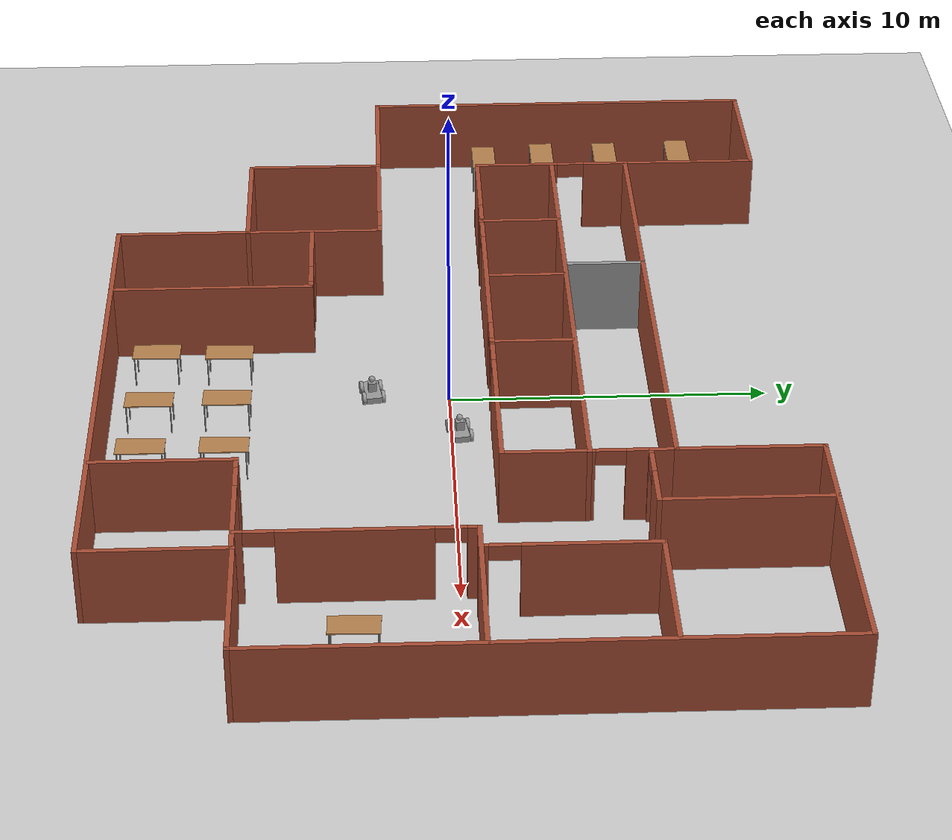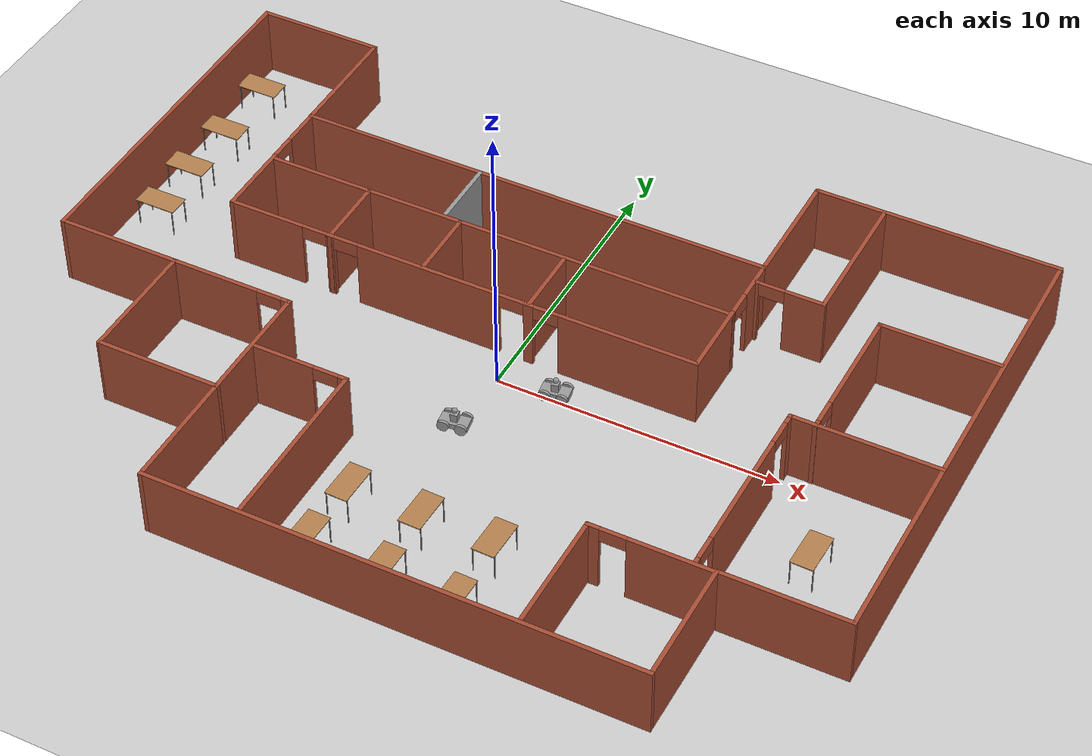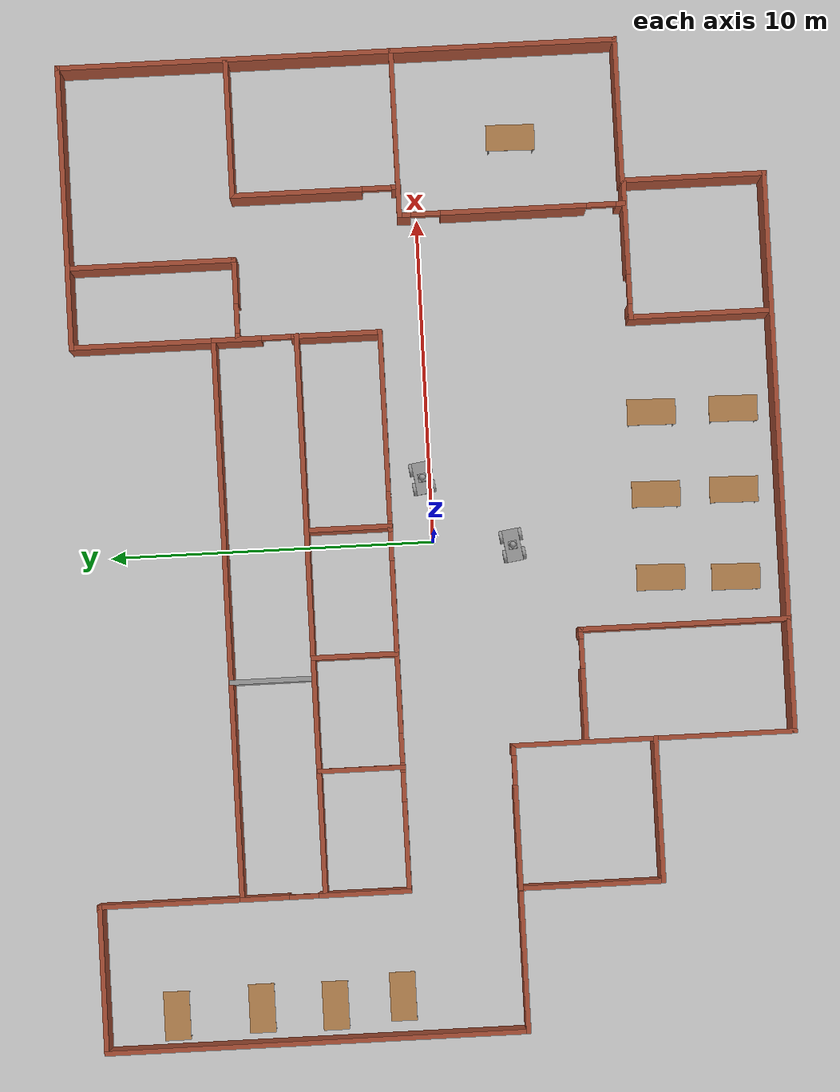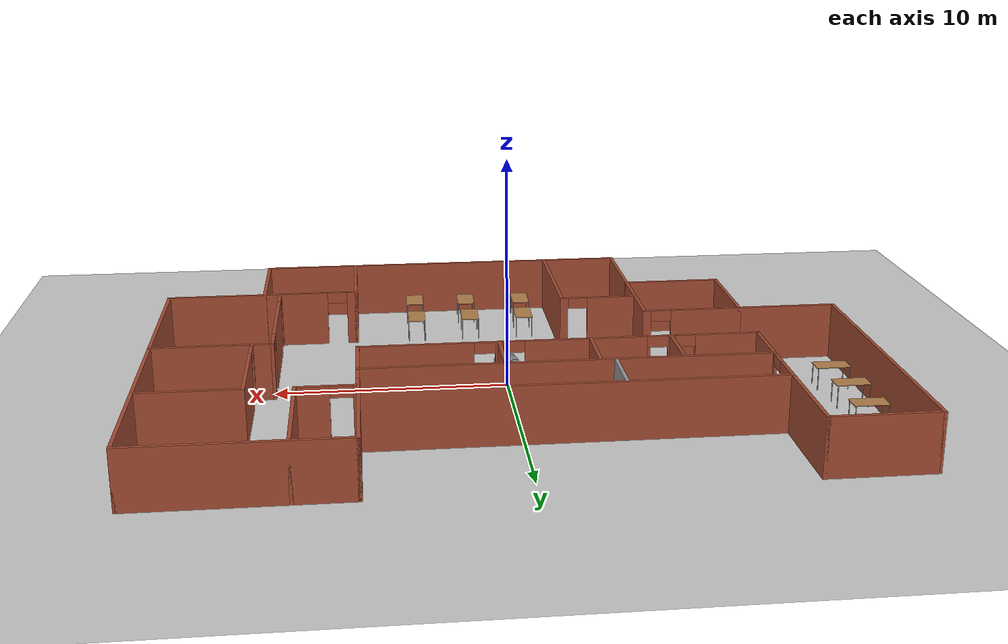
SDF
<sdf version="1.6">
 <world name="default">
  <plugin name="hello" filename="libhello.so"/>
  <light name="sun" type="directional">
   <pose>0 0 10 0 -0 0</pose>
   <diffuse>0.8 0.8 0.8 1</diffuse>
   <specular>0.2 0.2 0.2 1</specular>
   <attenuation>
    <range>1000</range>
    <constant>0.9</constant>
    <linear>0.01</linear>
    <quadratic>0.001</quadratic>
   </attenuation>
   <direction>-0.5 0.1 -0.9</direction>
  </light>
  <model name="ground_plane">
   <static>1</static>
   <link name="link">
    <collision name="collision">
     <geometry><plane><normal>0 0 1</normal><size>100 100</size></plane></geometry>
     <surface>
      <contact><collide_bitmask>65535</collide_bitmask></contact>
      <friction><ode><mu>100</mu><mu2>50</mu2></ode></friction>
     </surface>
    </collision>
    <visual name="visual">
     <cast_shadows>0</cast_shadows>
     <geometry><plane><normal>0 0 1</normal><size>100 100</size></plane></geometry>
     <material>
      <script><uri>file://media/materials/scripts/gazebo.material</uri><name>Gazebo/Grey</name></script>
     </material>
    </visual>
   </link>
  </model>
  <gravity>0 0 -9.8</gravity>
  <magnetic_field>6e-06 2.3e-05 -4.2e-05</magnetic_field>
  <atmosphere type="adiabatic"/>
  <physics name="default_physics" default="0" type="ode">
   <max_step_size>0.001</max_step_size>
   <real_time_factor>1</real_time_factor>
   <real_time_update_rate>1000</real_time_update_rate>
  </physics>
  <scene><ambient>0.4 0.4 0.4 1</ambient><background>0.7 0.7 0.7 1</background><shadows>1</shadows></scene>
  <spherical_coordinates>
   <surface_model>EARTH_WGS84</surface_model>
   <latitude_deg>0</latitude_deg>
   <longitude_deg>0</longitude_deg>
   <elevation>0</elevation>
   <heading_deg>0</heading_deg>
  </spherical_coordinates>
  <model name="robot">
   <link name="link_0">
    <pose>0 0 -0.109999 0 -0 0</pose>
    <inertial>
     <mass>1</mass>
     <inertia>
      <ixx>0.166667</ixx>
      <ixy>0</ixy>
      <ixz>0</ixz>
      <iyy>0.166667</iyy>
      <iyz>0</iyz>
      <izz>0.166667</izz>
     </inertia>
    </inertial>
    <visual name="visual">
     <geometry><box><size>1 0.5 0.2</size></box></geometry>
     <material>
      <lighting>1</lighting>
      <script><uri>file://media/materials/scripts/gazebo.material</uri><name>Gazebo/Grey</name></script>
      <shader type="pixel"><normal_map>__default__</normal_map></shader>
      <ambient>0.3 0.3 0.3 1</ambient>
      <diffuse>0.7 0.7 0.7 1</diffuse>
      <specular>0.01 0.01 0.01 1</specular>
      <emissive>0 0 0 1</emissive>
     </material>
    </visual>
    <collision name="collision">
     <geometry><box><size>1 0.5 0.2</size></box></geometry>
     <surface>
      <friction>
       <ode><mu>1</mu><mu2>1</mu2><fdir1>0 0 0</fdir1><slip1>0</slip1><slip2>0</slip2></ode>
       <torsional>
        <coefficient>1</coefficient>
        <patch_radius>0</patch_radius>
        <surface_radius>0</surface_radius>
        <use_patch_radius>1</use_patch_radius>
        <ode><slip>0</slip></ode>
       </torsional>
      </friction>
      <bounce><restitution_coefficient>0</restitution_coefficient><threshold>1e+06</threshold></bounce>
      <contact>
       <collide_without_contact>0</collide_without_contact>
       <collide_without_contact_bitmask>1</collide_without_contact_bitmask>
       <collide_bitmask>1</collide_bitmask>
       <ode>
        <soft_cfm>0</soft_cfm>
        <soft_erp>0.2</soft_erp>
        <kp>1e+13</kp>
        <kd>1</kd>
        <max_vel>0.01</max_vel>
        <min_depth>0</min_depth>
       </ode>
       <bullet>
        <split_impulse>1</split_impulse>
        <split_impulse_penetration_threshold>-0.01</split_impulse_penetration_threshold>
        <soft_cfm>0</soft_cfm>
        <soft_erp>0.2</soft_erp>
        <kp>1e+13</kp>
        <kd>1</kd>
       </bullet>
      </contact>
     </surface>
    </collision>
   </link>
   <link name="link_1">
    <pose>-0.3 -0.300019 -0.090004 1.5707 -0 0</pose>
    <inertial>
     <mass>1</mass>
     <inertia><ixx>0.145833</ixx><ixy>0</ixy><ixz>0</ixz><iyy>0.145833</iyy><iyz>0</iyz><izz>0.125</izz></inertia>
    </inertial>
    <visual name="visual">
     <geometry><cylinder><radius>0.2</radius><length>0.1</length></cylinder></geometry>
     <material>
      <lighting>1</lighting>
      <script><uri>file://media/materials/scripts/gazebo.material</uri><name>Gazebo/Grey</name></script>
      <shader type="pixel"><normal_map>__default__</normal_map></shader>
      <ambient>0.3 0.3 0.3 1</ambient>
      <diffuse>0.7 0.7 0.7 1</diffuse>
      <specular>0.01 0.01 0.01 1</specular>
      <emissive>0 0 0 1</emissive>
     </material>
    </visual>
    <collision name="collision">
     <geometry><cylinder><radius>0.2</radius><length>0.1</length></cylinder></geometry>
     <surface>
      <friction>
       <ode><mu>1</mu><mu2>1</mu2><fdir1>0 0 0</fdir1><slip1>0</slip1><slip2>0</slip2></ode>
       <torsional>
        <coefficient>1</coefficient>
        <patch_radius>0</patch_radius>
        <surface_radius>0</surface_radius>
        <use_patch_radius>1</use_patch_radius>
        <ode><slip>0</slip></ode>
       </torsional>
      </friction>
      <bounce><restitution_coefficient>0</restitution_coefficient><threshold>1e+06</threshold></bounce>
      <contact>
       <collide_without_contact>0</collide_without_contact>
       <collide_without_contact_bitmask>1</collide_without_contact_bitmask>
       <collide_bitmask>1</collide_bitmask>
       <ode>
        <soft_cfm>0</soft_cfm>
        <soft_erp>0.2</soft_erp>
        <kp>1e+13</kp>
        <kd>1</kd>
        <max_vel>0.01</max_vel>
        <min_depth>0</min_depth>
       </ode>
       <bullet>
        <split_impulse>1</split_impulse>
        <split_impulse_penetration_threshold>-0.01</split_impulse_penetration_threshold>
        <soft_cfm>0</soft_cfm>
        <soft_erp>0.2</soft_erp>
        <kp>1e+13</kp>
        <kd>1</kd>
       </bullet>
      </contact>
     </surface>
    </collision>
   </link>
   <link name="link_1_clone">
    <pose>-0.3 0.300019 -0.109999 1.5707 -0 0</pose>
    <inertial>
     <mass>1</mass>
     <inertia><ixx>0.145833</ixx><ixy>0</ixy><ixz>0</ixz><iyy>0.145833</iyy><iyz>0</iyz><izz>0.125</izz></inertia>
    </inertial>
    <visual name="visual">
     <geometry><cylinder><radius>0.2</radius><length>0.1</length></cylinder></geometry>
     <material>
      <lighting>1</lighting>
      <script><uri>file://media/materials/scripts/gazebo.material</uri><name>Gazebo/Grey</name></script>
      <shader type="pixel"><normal_map>__default__</normal_map></shader>
      <ambient>0.3 0.3 0.3 1</ambient>
      <diffuse>0.7 0.7 0.7 1</diffuse>
      <specular>0.01 0.01 0.01 1</specular>
      <emissive>0 0 0 1</emissive>
     </material>
    </visual>
    <collision name="collision">
     <geometry><cylinder><radius>0.2</radius><length>0.1</length></cylinder></geometry>
     <surface>
      <friction>
       <ode><mu>1</mu><mu2>1</mu2><fdir1>0 0 0</fdir1><slip1>0</slip1><slip2>0</slip2></ode>
       <torsional>
        <coefficient>1</coefficient>
        <patch_radius>0</patch_radius>
        <surface_radius>0</surface_radius>
        <use_patch_radius>1</use_patch_radius>
        <ode><slip>0</slip></ode>
       </torsional>
      </friction>
      <bounce><restitution_coefficient>0</restitution_coefficient><threshold>1e+06</threshold></bounce>
      <contact>
       <collide_without_contact>0</collide_without_contact>
       <collide_without_contact_bitmask>1</collide_without_contact_bitmask>
       <collide_bitmask>1</collide_bitmask>
       <ode>
        <soft_cfm>0</soft_cfm>
        <soft_erp>0.2</soft_erp>
        <kp>1e+13</kp>
        <kd>1</kd>
        <max_vel>0.01</max_vel>
        <min_depth>0</min_depth>
       </ode>
       <bullet>
        <split_impulse>1</split_impulse>
        <split_impulse_penetration_threshold>-0.01</split_impulse_penetration_threshold>
        <soft_cfm>0</soft_cfm>
        <soft_erp>0.2</soft_erp>
        <kp>1e+13</kp>
        <kd>1</kd>
       </bullet>
      </contact>
     </surface>
    </collision>
   </link>
   <link name="link_1_clone_clone">
    <pose>0.3 -0.300019 -0.109999 1.5707 -0 0</pose>
    <inertial>
     <mass>1</mass>
     <inertia><ixx>0.145833</ixx><ixy>0</ixy><ixz>0</ixz><iyy>0.145833</iyy><iyz>0</iyz><izz>0.125</izz></inertia>
    </inertial>
    <visual name="visual">
     <geometry><cylinder><radius>0.2</radius><length>0.1</length></cylinder></geometry>
     <material>
      <lighting>1</lighting>
      <script><uri>file://media/materials/scripts/gazebo.material</uri><name>Gazebo/Grey</name></script>
      <shader type="pixel"><normal_map>__default__</normal_map></shader>
      <ambient>0.3 0.3 0.3 1</ambient>
      <diffuse>0.7 0.7 0.7 1</diffuse>
      <specular>0.01 0.01 0.01 1</specular>
      <emissive>0 0 0 1</emissive>
     </material>
    </visual>
    <collision name="collision">
     <geometry><cylinder><radius>0.2</radius><length>0.1</length></cylinder></geometry>
     <surface>
      <friction>
       <ode><mu>1</mu><mu2>1</mu2><fdir1>0 0 0</fdir1><slip1>0</slip1><slip2>0</slip2></ode>
       <torsional>
        <coefficient>1</coefficient>
        <patch_radius>0</patch_radius>
        <surface_radius>0</surface_radius>
        <use_patch_radius>1</use_patch_radius>
        <ode><slip>0</slip></ode>
       </torsional>
      </friction>
      <bounce><restitution_coefficient>0</restitution_coefficient><threshold>1e+06</threshold></bounce>
      <contact>
       <collide_without_contact>0</collide_without_contact>
       <collide_without_contact_bitmask>1</collide_without_contact_bitmask>
       <collide_bitmask>1</collide_bitmask>
       <ode>
        <soft_cfm>0</soft_cfm>
        <soft_erp>0.2</soft_erp>
        <kp>1e+13</kp>
        <kd>1</kd>
        <max_vel>0.01</max_vel>
        <min_depth>0</min_depth>
       </ode>
       <bullet>
        <split_impulse>1</split_impulse>
        <split_impulse_penetration_threshold>-0.01</split_impulse_penetration_threshold>
        <soft_cfm>0</soft_cfm>
        <soft_erp>0.2</soft_erp>
        <kp>1e+13</kp>
        <kd>1</kd>
       </bullet>
      </contact>
     </surface>
    </collision>
   </link>
   <link name="link_1_clone_clone_clone">
    <pose>0.3 0.300019 -0.109999 1.5707 -0 0</pose>
    <inertial>
     <mass>1</mass>
     <inertia><ixx>0.145833</ixx><ixy>0</ixy><ixz>0</ixz><iyy>0.145833</iyy><iyz>0</iyz><izz>0.125</izz></inertia>
    </inertial>
    <visual name="visual">
     <geometry><cylinder><radius>0.2</radius><length>0.1</length></cylinder></geometry>
     <material>
      <lighting>1</lighting>
      <script><uri>file://media/materials/scripts/gazebo.material</uri><name>Gazebo/Grey</name></script>
      <shader type="pixel"><normal_map>__default__</normal_map></shader>
      <ambient>0.3 0.3 0.3 1</ambient>
      <diffuse>0.7 0.7 0.7 1</diffuse>
      <specular>0.01 0.01 0.01 1</specular>
      <emissive>0 0 0 1</emissive>
     </material>
    </visual>
    <collision name="collision">
     <geometry><cylinder><radius>0.2</radius><length>0.1</length></cylinder></geometry>
     <surface>
      <friction>
       <ode><mu>1</mu><mu2>1</mu2><fdir1>0 0 0</fdir1><slip1>0</slip1><slip2>0</slip2></ode>
       <torsional>
        <coefficient>1</coefficient>
        <patch_radius>0</patch_radius>
        <surface_radius>0</surface_radius>
        <use_patch_radius>1</use_patch_radius>
        <ode><slip>0</slip></ode>
       </torsional>
      </friction>
      <bounce><restitution_coefficient>0</restitution_coefficient><threshold>1e+06</threshold></bounce>
      <contact>
       <collide_without_contact>0</collide_without_contact>
       <collide_without_contact_bitmask>1</collide_without_contact_bitmask>
       <collide_bitmask>1</collide_bitmask>
       <ode>
        <soft_cfm>0</soft_cfm>
        <soft_erp>0.2</soft_erp>
        <kp>1e+13</kp>
        <kd>1</kd>
        <max_vel>0.01</max_vel>
        <min_depth>0</min_depth>
       </ode>
       <bullet>
        <split_impulse>1</split_impulse>
        <split_impulse_penetration_threshold>-0.01</split_impulse_penetration_threshold>
        <soft_cfm>0</soft_cfm>
        <soft_erp>0.2</soft_erp>
        <kp>1e+13</kp>
        <kd>1</kd>
       </bullet>
      </contact>
     </surface>
    </collision>
   </link>
   <link name="link_2">
    <pose>-0 0 0.140001 0 -0 0</pose>
    <inertial>
     <mass>1</mass>
     <inertia>
      <ixx>0.166667</ixx>
      <ixy>0</ixy>
      <ixz>0</ixz>
      <iyy>0.166667</iyy>
      <iyz>0</iyz>
      <izz>0.166667</izz>
     </inertia>
    </inertial>
    <visual name="visual">
     <geometry><box><size>0.25 0.25 0.3</size></box></geometry>
     <material>
      <lighting>1</lighting>
      <script><uri>file://media/materials/scripts/gazebo.material</uri><name>Gazebo/Grey</name></script>
      <shader type="pixel"><normal_map>__default__</normal_map></shader>
      <ambient>0.3 0.3 0.3 1</ambient>
      <diffuse>0.7 0.7 0.7 1</diffuse>
      <specular>0.01 0.01 0.01 1</specular>
      <emissive>0 0 0 1</emissive>
     </material>
    </visual>
    <collision name="collision">
     <geometry><box><size>0.25 0.25 0.3</size></box></geometry>
     <surface>
      <friction>
       <ode><mu>1</mu><mu2>1</mu2><fdir1>0 0 0</fdir1><slip1>0</slip1><slip2>0</slip2></ode>
       <torsional>
        <coefficient>1</coefficient>
        <patch_radius>0</patch_radius>
        <surface_radius>0</surface_radius>
        <use_patch_radius>1</use_patch_radius>
        <ode><slip>0</slip></ode>
       </torsional>
      </friction>
      <bounce><restitution_coefficient>0</restitution_coefficient><threshold>1e+06</threshold></bounce>
      <contact>
       <collide_without_contact>0</collide_without_contact>
       <collide_without_contact_bitmask>1</collide_without_contact_bitmask>
       <collide_bitmask>1</collide_bitmask>
       <ode>
        <soft_cfm>0</soft_cfm>
        <soft_erp>0.2</soft_erp>
        <kp>1e+13</kp>
        <kd>1</kd>
        <max_vel>0.01</max_vel>
        <min_depth>0</min_depth>
       </ode>
       <bullet>
        <split_impulse>1</split_impulse>
        <split_impulse_penetration_threshold>-0.01</split_impulse_penetration_threshold>
        <soft_cfm>0</soft_cfm>
        <soft_erp>0.2</soft_erp>
        <kp>1e+13</kp>
        <kd>1</kd>
       </bullet>
      </contact>
     </surface>
    </collision>
   </link>
   <link name="link_3">
    <pose>-0 0 0.390001 0 -0 0</pose>
    <inertial>
     <mass>1</mass>
     <inertia><ixx>0.1</ixx><ixy>0</ixy><ixz>0</ixz><iyy>0.1</iyy><iyz>0</iyz><izz>0.1</izz></inertia>
    </inertial>
    <visual name="visual">
     <geometry><sphere><radius>0.1</radius></sphere></geometry>
     <material>
      <lighting>1</lighting>
      <script><uri>file://media/materials/scripts/gazebo.material</uri><name>Gazebo/Grey</name></script>
      <shader type="pixel"><normal_map>__default__</normal_map></shader>
      <ambient>0.3 0.3 0.3 1</ambient>
      <diffuse>0.7 0.7 0.7 1</diffuse>
      <specular>0.01 0.01 0.01 1</specular>
      <emissive>0 0 0 1</emissive>
     </material>
    </visual>
    <collision name="collision">
     <geometry><sphere><radius>0.1</radius></sphere></geometry>
     <surface>
      <friction>
       <ode><mu>1</mu><mu2>1</mu2><fdir1>0 0 0</fdir1><slip1>0</slip1><slip2>0</slip2></ode>
       <torsional>
        <coefficient>1</coefficient>
        <patch_radius>0</patch_radius>
        <surface_radius>0</surface_radius>
        <use_patch_radius>1</use_patch_radius>
        <ode><slip>0</slip></ode>
       </torsional>
      </friction>
      <bounce><restitution_coefficient>0</restitution_coefficient><threshold>1e+06</threshold></bounce>
      <contact>
       <collide_without_contact>0</collide_without_contact>
       <collide_without_contact_bitmask>1</collide_without_contact_bitmask>
       <collide_bitmask>1</collide_bitmask>
       <ode>
        <soft_cfm>0</soft_cfm>
        <soft_erp>0.2</soft_erp>
        <kp>1e+13</kp>
        <kd>1</kd>
        <max_vel>0.01</max_vel>
        <min_depth>0</min_depth>
       </ode>
       <bullet>
        <split_impulse>1</split_impulse>
        <split_impulse_penetration_threshold>-0.01</split_impulse_penetration_threshold>
        <soft_cfm>0</soft_cfm>
        <soft_erp>0.2</soft_erp>
        <kp>1e+13</kp>
        <kd>1</kd>
       </bullet>
      </contact>
     </surface>
    </collision>
   </link>
   <joint name="link_0_JOINT_0_0" type="fixed">
    <parent>link_0</parent>
    <child>link_2</child>
    <physics>
     <ode><limit><cfm>0</cfm><erp>0.2</erp></limit><suspension><cfm>0</cfm><erp>0.2</erp></suspension></ode>
    </physics>
   </joint>
   <joint name="link_0_JOINT_0" type="revolute">
    <parent>link_0</parent>
    <child>link_1</child>
    <axis>
     <xyz>0 0 1</xyz>
     <use_parent_model_frame>0</use_parent_model_frame>
     <limit>
      <lower>-1.79769e+308</lower>
      <upper>1.79769e+308</upper>
      <effort>-1</effort>
      <velocity>-1</velocity>
     </limit>
     <dynamics>
      <spring_reference>0</spring_reference>
      <spring_stiffness>0</spring_stiffness>
      <damping>0</damping>
      <friction>0</friction>
     </dynamics>
    </axis>
    <physics>
     <ode><limit><cfm>0</cfm><erp>0.2</erp></limit><suspension><cfm>0</cfm><erp>0.2</erp></suspension></ode>
    </physics>
   </joint>
   <joint name="link_0_JOINT_1" type="revolute">
    <parent>link_0</parent>
    <child>link_1</child>
    <axis>
     <xyz>0 0 1</xyz>
     <use_parent_model_frame>0</use_parent_model_frame>
     <limit>
      <lower>-1.79769e+308</lower>
      <upper>1.79769e+308</upper>
      <effort>-1</effort>
      <velocity>-1</velocity>
     </limit>
     <dynamics>
      <spring_reference>0</spring_reference>
      <spring_stiffness>0</spring_stiffness>
      <damping>0</damping>
      <friction>0</friction>
     </dynamics>
    </axis>
    <physics>
     <ode><limit><cfm>0</cfm><erp>0.2</erp></limit><suspension><cfm>0</cfm><erp>0.2</erp></suspension></ode>
    </physics>
   </joint>
   <joint name="link_0_JOINT_2" type="revolute">
    <parent>link_0</parent>
    <child>link_1_clone</child>
    <axis>
     <xyz>0 0 -1</xyz>
     <use_parent_model_frame>0</use_parent_model_frame>
     <limit>
      <lower>-1.79769e+308</lower>
      <upper>1.79769e+308</upper>
      <effort>-1</effort>
      <velocity>-1</velocity>
     </limit>
     <dynamics>
      <spring_reference>0</spring_reference>
      <spring_stiffness>0</spring_stiffness>
      <damping>0</damping>
      <friction>0</friction>
     </dynamics>
    </axis>
    <physics>
     <ode><limit><cfm>0</cfm><erp>0.2</erp></limit><suspension><cfm>0</cfm><erp>0.2</erp></suspension></ode>
    </physics>
   </joint>
   <joint name="link_0_JOINT_3" type="revolute">
    <parent>link_0</parent>
    <child>link_1_clone_clone</child>
    <axis>
     <xyz>0 0 1</xyz>
     <use_parent_model_frame>0</use_parent_model_frame>
     <limit>
      <lower>-1.79769e+308</lower>
      <upper>1.79769e+308</upper>
      <effort>-1</effort>
      <velocity>-1</velocity>
     </limit>
     <dynamics>
      <spring_reference>0</spring_reference>
      <spring_stiffness>0</spring_stiffness>
      <damping>0</damping>
      <friction>0</friction>
     </dynamics>
    </axis>
    <physics>
     <ode><limit><cfm>0</cfm><erp>0.2</erp></limit><suspension><cfm>0</cfm><erp>0.2</erp></suspension></ode>
    </physics>
   </joint>
   <joint name="link_0_JOINT_4" type="revolute">
    <parent>link_0</parent>
    <child>link_1_clone_clone_clone</child>
    <axis>
     <xyz>0 0 -1</xyz>
     <use_parent_model_frame>0</use_parent_model_frame>
     <limit>
      <lower>-1.79769e+308</lower>
      <upper>1.79769e+308</upper>
      <effort>-1</effort>
      <velocity>-1</velocity>
     </limit>
     <dynamics>
      <spring_reference>0</spring_reference>
      <spring_stiffness>0</spring_stiffness>
      <damping>0</damping>
      <friction>0</friction>
     </dynamics>
    </axis>
    <physics>
     <ode><limit><cfm>0</cfm><erp>0.2</erp></limit><suspension><cfm>0</cfm><erp>0.2</erp></suspension></ode>
    </physics>
   </joint>
   <joint name="link_2_JOINT_5" type="ball">
    <parent>link_2</parent>
    <child>link_3</child>
    <physics>
     <ode><limit><cfm>0</cfm><erp>0.2</erp></limit><suspension><cfm>0</cfm><erp>0.2</erp></suspension></ode>
    </physics>
   </joint>
   <static>0</static>
   <pose>2.0016 0.24432 0.309995 0.000104 -9e-05 0.151933</pose>
  </model>
  <model name="mybuilding">
   <pose>-0.044618 0.031992 0 0 -0 0</pose>
   <link name="Wall_0">
    <collision name="Wall_0_Collision">
     <geometry><box><size>4.5 0.15 2.5</size></box></geometry>
     <pose>0 0 1.25 0 -0 0</pose>
    </collision>
    <visual name="Wall_0_Visual">
     <pose>0 0 1.25 0 -0 0</pose>
     <geometry><box><size>4.5 0.15 2.5</size></box></geometry>
     <material>
      <script><uri>file://media/materials/scripts/gazebo.material</uri><name>Gazebo/Bricks</name></script>
      <ambient>1 1 1 1</ambient>
     </material>
     <meta><layer>0</layer></meta>
    </visual>
    <pose>-12.8 10.725 0 0 -0 0</pose>
   </link>
   <link name="Wall_1">
    <collision name="Wall_1_Collision">
     <geometry><box><size>4.5 0.15 2.5</size></box></geometry>
     <pose>0 0 1.25 0 -0 0</pose>
    </collision>
    <visual name="Wall_1_Visual">
     <pose>0 0 1.25 0 -0 0</pose>
     <geometry><box><size>4.5 0.15 2.5</size></box></geometry>
     <material>
      <script><uri>file://media/materials/scripts/gazebo.material</uri><name>Gazebo/Bricks</name></script>
      <ambient>1 1 1 1</ambient>
     </material>
     <meta><layer>0</layer></meta>
    </visual>
    <pose>-10.625 8.55 0 0 0 -1.5708</pose>
   </link>
   <link name="Wall_16">
    <collision name="Wall_16_Collision">
     <geometry><box><size>13 0.15 2.5</size></box></geometry>
     <pose>0 0 1.25 0 -0 0</pose>
    </collision>
    <visual name="Wall_16_Visual">
     <pose>0 0 1.25 0 -0 0</pose>
     <geometry><box><size>13 0.15 2.5</size></box></geometry>
     <material>
      <script><uri>file://media/materials/scripts/gazebo.material</uri><name>Gazebo/Bricks</name></script>
      <ambient>1 1 1 1</ambient>
     </material>
     <meta><layer>0</layer></meta>
    </visual>
    <pose>-15.075 4.3 0 0 -0 1.5708</pose>
   </link>
   <link name="Wall_2">
    <collision name="Wall_2_Collision">
     <geometry><box><size>17.25 0.15 2.5</size></box></geometry>
     <pose>0 0 1.25 0 -0 0</pose>
    </collision>
    <visual name="Wall_2_Visual">
     <pose>0 0 1.25 0 -0 0</pose>
     <geometry><box><size>17.25 0.15 2.5</size></box></geometry>
     <material>
      <script><uri>file://media/materials/scripts/gazebo.material</uri><name>Gazebo/Bricks</name></script>
      <ambient>1 1 1 1</ambient>
     </material>
     <meta><layer>0</layer></meta>
    </visual>
    <pose>-2.075 6.375 0 0 -0 0</pose>
   </link>
   <link name="Wall_20">
    <collision name="Wall_20_Collision">
     <geometry><box><size>4.5 0.15 2.5</size></box></geometry>
     <pose>0 0 1.25 0 -0 0</pose>
    </collision>
    <visual name="Wall_20_Visual">
     <pose>0 0 1.25 0 -0 0</pose>
     <geometry><box><size>4.5 0.15 2.5</size></box></geometry>
     <material>
      <script><uri>file://media/materials/scripts/gazebo.material</uri><name>Gazebo/Bricks</name></script>
      <ambient>1 1 1 1</ambient>
     </material>
     <meta><layer>0</layer></meta>
    </visual>
    <pose>-12.9 -2.125 0 0 -0 0</pose>
   </link>
   <link name="Wall_21">
    <collision name="Wall_21_Collision">
     <geometry><box><size>4.5 0.15 2.5</size></box></geometry>
     <pose>0 0 1.25 0 -0 0</pose>
    </collision>
    <visual name="Wall_21_Visual">
     <pose>0 0 1.25 0 -0 0</pose>
     <geometry><box><size>4.5 0.15 2.5</size></box></geometry>
     <material>
      <script><uri>file://media/materials/scripts/gazebo.material</uri><name>Gazebo/Bricks</name></script>
      <ambient>1 1 1 1</ambient>
     </material>
     <meta><layer>0</layer></meta>
    </visual>
    <pose>-10.725 -4.3 0 0 0 -1.5708</pose>
   </link>
   <link name="Wall_22">
    <collision name="Wall_22_Collision">
     <geometry><box><size>4.5 0.15 2.5</size></box></geometry>
     <pose>0 0 1.25 0 -0 0</pose>
    </collision>
    <visual name="Wall_22_Visual">
     <pose>0 0 1.25 0 -0 0</pose>
     <geometry><box><size>4.5 0.15 2.5</size></box></geometry>
     <material>
      <script><uri>file://media/materials/scripts/gazebo.material</uri><name>Gazebo/Bricks</name></script>
      <ambient>1 1 1 1</ambient>
     </material>
     <meta><layer>0</layer></meta>
    </visual>
    <pose>-8.55 -6.475 0 0 -0 0</pose>
   </link>
   <link name="Wall_24">
    <pose>-10.625 3.825 0 0 0 -1.5708</pose>
    <visual name="Wall_24_Visual_0">
     <pose>-1.86673 0 1.25 0 -0 0</pose>
     <geometry><box><size>1.51653 0.15 2.5</size></box></geometry>
     <material>
      <script><uri>file://media/materials/scripts/gazebo.material</uri><name>Gazebo/Bricks</name></script>
      <ambient>1 1 1 1</ambient>
     </material>
     <meta><layer>0</layer></meta>
    </visual>
    <collision name="Wall_24_Collision_0">
     <geometry><box><size>1.51653 0.15 2.5</size></box></geometry>
     <pose>-1.86673 0 1.25 0 -0 0</pose>
    </collision>
    <visual name="Wall_24_Visual_1">
     <pose>1.20827 0 1.25 0 -0 0</pose>
     <geometry><box><size>2.83347 0.15 2.5</size></box></geometry>
     <material>
      <script><uri>file://media/materials/scripts/gazebo.material</uri><name>Gazebo/Bricks</name></script>
      <ambient>1 1 1 1</ambient>
     </material>
     <meta><layer>0</layer></meta>
    </visual>
    <collision name="Wall_24_Collision_1">
     <geometry><box><size>2.83347 0.15 2.5</size></box></geometry>
     <pose>1.20827 0 1.25 0 -0 0</pose>
    </collision>
    <visual name="Wall_24_Visual_2">
     <pose>-0.658467 0 2.25 0 -0 0</pose>
     <geometry><box><size>0.9 0.15 0.5</size></box></geometry>
     <material>
      <script><uri>file://media/materials/scripts/gazebo.material</uri><name>Gazebo/Bricks</name></script>
      <ambient>1 1 1 1</ambient>
     </material>
     <meta><layer>0</layer></meta>
    </visual>
    <collision name="Wall_24_Collision_2">
     <geometry><box><size>0.9 0.15 0.5</size></box></geometry>
     <pose>-0.658467 0 2.25 0 -0 0</pose>
    </collision>
   </link>
   <link name="Wall_25">
    <pose>-2.075 1.275 0 0 -0 0</pose>
    <visual name="Wall_25_Visual_0">
     <pose>-7.22106 0 1.25 0 -0 0</pose>
     <geometry><box><size>2.80789 0.15 2.5</size></box></geometry>
     <material>
      <script><uri>file://media/materials/scripts/gazebo.material</uri><name>Gazebo/Bricks</name></script>
      <ambient>1 1 1 1</ambient>
     </material>
     <meta><layer>0</layer></meta>
    </visual>
    <collision name="Wall_25_Collision_0">
     <geometry><box><size>2.80789 0.15 2.5</size></box></geometry>
     <pose>-7.22106 0 1.25 0 -0 0</pose>
    </collision>
    <visual name="Wall_25_Visual_1">
     <pose>-4.77525 0 1.25 0 -0 0</pose>
     <geometry><box><size>0.283739 0.15 2.5</size></box></geometry>
     <material>
      <script><uri>file://media/materials/scripts/gazebo.material</uri><name>Gazebo/Bricks</name></script>
      <ambient>1 1 1 1</ambient>
     </material>
     <meta><layer>0</layer></meta>
    </visual>
    <collision name="Wall_25_Collision_1">
     <geometry><box><size>0.283739 0.15 2.5</size></box></geometry>
     <pose>-4.77525 0 1.25 0 -0 0</pose>
    </collision>
    <visual name="Wall_25_Visual_2">
     <pose>-1.10296 0 1.25 0 -0 0</pose>
     <geometry><box><size>5.26082 0.15 2.5</size></box></geometry>
     <material>
      <script><uri>file://media/materials/scripts/gazebo.material</uri><name>Gazebo/Bricks</name></script>
      <ambient>1 1 1 1</ambient>
     </material>
     <meta><layer>0</layer></meta>
    </visual>
    <collision name="Wall_25_Collision_2">
     <geometry><box><size>5.26082 0.15 2.5</size></box></geometry>
     <pose>-1.10296 0 1.25 0 -0 0</pose>
    </collision>
    <visual name="Wall_25_Visual_3">
     <pose>2.59622 0 1.25 0 -0 0</pose>
     <geometry><box><size>0.337545 0.15 2.5</size></box></geometry>
     <material>
      <script><uri>file://media/materials/scripts/gazebo.material</uri><name>Gazebo/Bricks</name></script>
      <ambient>1 1 1 1</ambient>
     </material>
     <meta><layer>0</layer></meta>
    </visual>
    <collision name="Wall_25_Collision_3">
     <geometry><box><size>0.337545 0.15 2.5</size></box></geometry>
     <pose>2.59622 0 1.25 0 -0 0</pose>
    </collision>
    <visual name="Wall_25_Visual_4">
     <pose>6.145 0 1.25 0 -0 0</pose>
     <geometry><box><size>4.96001 0.15 2.5</size></box></geometry>
     <material>
      <script><uri>file://media/materials/scripts/gazebo.material</uri><name>Gazebo/Bricks</name></script>
      <ambient>1 1 1 1</ambient>
     </material>
     <meta><layer>0</layer></meta>
    </visual>
    <collision name="Wall_25_Collision_4">
     <geometry><box><size>4.96001 0.15 2.5</size></box></geometry>
     <pose>6.145 0 1.25 0 -0 0</pose>
    </collision>
    <visual name="Wall_25_Visual_5">
     <pose>-5.36712 0 2.25 0 -0 0</pose>
     <geometry><box><size>0.9 0.15 0.5</size></box></geometry>
     <material>
      <script><uri>file://media/materials/scripts/gazebo.material</uri><name>Gazebo/Bricks</name></script>
      <ambient>1 1 1 1</ambient>
     </material>
     <meta><layer>0</layer></meta>
    </visual>
    <collision name="Wall_25_Collision_5">
     <geometry><box><size>0.9 0.15 0.5</size></box></geometry>
     <pose>-5.36712 0 2.25 0 -0 0</pose>
    </collision>
    <visual name="Wall_25_Visual_6">
     <pose>-4.18338 0 2.25 0 -0 0</pose>
     <geometry><box><size>0.9 0.15 0.5</size></box></geometry>
     <material>
      <script><uri>file://media/materials/scripts/gazebo.material</uri><name>Gazebo/Bricks</name></script>
      <ambient>1 1 1 1</ambient>
     </material>
     <meta><layer>0</layer></meta>
    </visual>
    <collision name="Wall_25_Collision_6">
     <geometry><box><size>0.9 0.15 0.5</size></box></geometry>
     <pose>-4.18338 0 2.25 0 -0 0</pose>
    </collision>
    <visual name="Wall_25_Visual_7">
     <pose>1.97745 0 2.25 0 -0 0</pose>
     <geometry><box><size>0.9 0.15 0.5</size></box></geometry>
     <material>
      <script><uri>file://media/materials/scripts/gazebo.material</uri><name>Gazebo/Bricks</name></script>
      <ambient>1 1 1 1</ambient>
     </material>
     <meta><layer>0</layer></meta>
    </visual>
    <collision name="Wall_25_Collision_7">
     <geometry><box><size>0.9 0.15 0.5</size></box></geometry>
     <pose>1.97745 0 2.25 0 -0 0</pose>
    </collision>
    <visual name="Wall_25_Visual_8">
     <pose>3.21499 0 2.25 0 -0 0</pose>
     <geometry><box><size>0.9 0.15 0.5</size></box></geometry>
     <material>
      <script><uri>file://media/materials/scripts/gazebo.material</uri><name>Gazebo/Bricks</name></script>
      <ambient>1 1 1 1</ambient>
     </material>
     <meta><layer>0</layer></meta>
    </visual>
    <collision name="Wall_25_Collision_8">
     <geometry><box><size>0.9 0.15 0.5</size></box></geometry>
     <pose>3.21499 0 2.25 0 -0 0</pose>
    </collision>
   </link>
   <link name="Wall_26">
    <pose>6.475 3.825 0 0 -0 1.5708</pose>
    <visual name="Wall_26_Visual_0">
     <pose>-1.22172 0 1.25 0 -0 0</pose>
     <geometry><box><size>2.80656 0.15 2.5</size></box></geometry>
     <material>
      <script><uri>file://media/materials/scripts/gazebo.material</uri><name>Gazebo/Bricks</name></script>
      <ambient>1 1 1 1</ambient>
     </material>
     <meta><layer>0</layer></meta>
    </visual>
    <collision name="Wall_26_Collision_0">
     <geometry><box><size>2.80656 0.15 2.5</size></box></geometry>
     <pose>-1.22172 0 1.25 0 -0 0</pose>
    </collision>
    <visual name="Wall_26_Visual_1">
     <pose>1.85328 0 1.25 0 -0 0</pose>
     <geometry><box><size>1.54344 0.15 2.5</size></box></geometry>
     <material>
      <script><uri>file://media/materials/scripts/gazebo.material</uri><name>Gazebo/Bricks</name></script>
      <ambient>1 1 1 1</ambient>
     </material>
     <meta><layer>0</layer></meta>
    </visual>
    <collision name="Wall_26_Collision_1">
     <geometry><box><size>1.54344 0.15 2.5</size></box></geometry>
     <pose>1.85328 0 1.25 0 -0 0</pose>
    </collision>
    <visual name="Wall_26_Visual_2">
     <pose>0.631564 0 2.25 0 -0 0</pose>
     <geometry><box><size>0.9 0.15 0.5</size></box></geometry>
     <material>
      <script><uri>file://media/materials/scripts/gazebo.material</uri><name>Gazebo/Bricks</name></script>
      <ambient>1 1 1 1</ambient>
     </material>
     <meta><layer>0</layer></meta>
    </visual>
    <collision name="Wall_26_Collision_2">
     <geometry><box><size>0.9 0.15 0.5</size></box></geometry>
     <pose>0.631564 0 2.25 0 -0 0</pose>
    </collision>
   </link>
   <link name="Wall_28">
    <collision name="Wall_28_Collision">
     <geometry><box><size>17.25 0.15 2.5</size></box></geometry>
     <pose>0 0 1.25 0 -0 0</pose>
    </collision>
    <visual name="Wall_28_Visual">
     <pose>0 0 1.25 0 -0 0</pose>
     <geometry><box><size>17.25 0.15 2.5</size></box></geometry>
     <material>
      <script><uri>file://media/materials/scripts/gazebo.material</uri><name>Gazebo/Bricks</name></script>
      <ambient>1 1 1 1</ambient>
     </material>
     <meta><layer>0</layer></meta>
    </visual>
    <pose>-2.06669 3.83779 0 0 -0 0</pose>
   </link>
   <link name="Wall_3">
    <collision name="Wall_3_Collision">
     <geometry><box><size>4.5 0.15 2.5</size></box></geometry>
     <pose>0 0 1.25 0 -0 0</pose>
    </collision>
    <visual name="Wall_3_Visual">
     <pose>0 0 1.25 0 -0 0</pose>
     <geometry><box><size>4.5 0.15 2.5</size></box></geometry>
     <material>
      <script><uri>file://media/materials/scripts/gazebo.material</uri><name>Gazebo/Bricks</name></script>
      <ambient>1 1 1 1</ambient>
     </material>
     <meta><layer>0</layer></meta>
    </visual>
    <pose>6.475 8.55 0 0 -0 1.5708</pose>
   </link>
   <link name="Wall_30">
    <collision name="Wall_30_Collision">
     <geometry><box><size>2.5 0.15 2.5</size></box></geometry>
     <pose>0 0 1.25 0 -0 0</pose>
    </collision>
    <visual name="Wall_30_Visual">
     <pose>0 0 1.25 0 -0 0</pose>
     <geometry><box><size>2.5 0.15 2.5</size></box></geometry>
     <material>
      <script><uri>file://media/materials/scripts/gazebo.material</uri><name>Gazebo/Grey</name></script>
      <ambient>1 1 1 1</ambient>
     </material>
     <meta><layer>0</layer></meta>
    </visual>
    <pose>-3.99851 5.16479 0 0 0 -1.5708</pose>
   </link>
   <link name="Wall_33">
    <collision name="Wall_33_Collision">
     <geometry><box><size>2.7 0.15 2.5</size></box></geometry>
     <pose>0 0 1.25 0 -0 0</pose>
    </collision>
    <visual name="Wall_33_Visual">
     <pose>0 0 1.25 0 -0 0</pose>
     <geometry><box><size>2.7 0.15 2.5</size></box></geometry>
     <material>
      <script><uri>file://media/materials/scripts/gazebo.material</uri><name>Gazebo/Bricks</name></script>
      <ambient>1 1 1 1</ambient>
     </material>
     <meta><layer>0</layer></meta>
    </visual>
    <pose>-6.85025 2.53589 0 0 0 -1.5708</pose>
   </link>
   <link name="Wall_35">
    <collision name="Wall_35_Collision">
     <geometry><box><size>2.7 0.15 2.5</size></box></geometry>
     <pose>0 0 1.25 0 -0 0</pose>
    </collision>
    <visual name="Wall_35_Visual">
     <pose>0 0 1.25 0 -0 0</pose>
     <geometry><box><size>2.7 0.15 2.5</size></box></geometry>
     <material>
      <script><uri>file://media/materials/scripts/gazebo.material</uri><name>Gazebo/Bricks</name></script>
      <ambient>1 1 1 1</ambient>
     </material>
     <meta><layer>0</layer></meta>
    </visual>
    <pose>-3.37974 2.56279 0 0 0 -1.5708</pose>
   </link>
   <link name="Wall_37">
    <collision name="Wall_37_Collision">
     <geometry><box><size>2.7 0.15 2.5</size></box></geometry>
     <pose>0 0 1.25 0 -0 0</pose>
    </collision>
    <visual name="Wall_37_Visual">
     <pose>0 0 1.25 0 -0 0</pose>
     <geometry><box><size>2.7 0.15 2.5</size></box></geometry>
     <material>
      <script><uri>file://media/materials/scripts/gazebo.material</uri><name>Gazebo/Bricks</name></script>
      <ambient>1 1 1 1</ambient>
     </material>
     <meta><layer>0</layer></meta>
    </visual>
    <pose>0.52122 2.56279 0 0 0 -1.5708</pose>
   </link>
   <link name="Wall_39">
    <collision name="Wall_39_Collision">
     <geometry><box><size>5.25 0.15 2.5</size></box></geometry>
     <pose>0 0 1.25 0 -0 0</pose>
    </collision>
    <visual name="Wall_39_Visual">
     <pose>0 0 1.25 0 -0 0</pose>
     <geometry><box><size>5.25 0.15 2.5</size></box></geometry>
     <material>
      <script><uri>file://media/materials/scripts/gazebo.material</uri><name>Gazebo/Bricks</name></script>
      <ambient>1 1 1 1</ambient>
     </material>
     <meta><layer>0</layer></meta>
    </visual>
    <pose>8.91501 8.175 0 0 0 -1.5708</pose>
   </link>
   <link name="Wall_4">
    <collision name="Wall_4_Collision">
     <geometry><box><size>8.75 0.15 2.5</size></box></geometry>
     <pose>0 0 1.25 0 -0 0</pose>
    </collision>
    <visual name="Wall_4_Visual">
     <pose>0 0 1.25 0 -0 0</pose>
     <geometry><box><size>8.75 0.15 2.5</size></box></geometry>
     <material>
      <script><uri>file://media/materials/scripts/gazebo.material</uri><name>Gazebo/Bricks</name></script>
      <ambient>1 1 1 1</ambient>
     </material>
     <meta><layer>0</layer></meta>
    </visual>
    <pose>10.775 10.725 0 0 -0 0</pose>
   </link>
   <link name="Wall_40">
    <pose>7.74001 5.625 0 0 -0 3.14159</pose>
    <visual name="Wall_40_Visual_0">
     <pose>-0.536244 0 1.25 0 -0 0</pose>
     <geometry><box><size>1.42751 0.15 2.5</size></box></geometry>
     <material>
      <script><uri>file://media/materials/scripts/gazebo.material</uri><name>Gazebo/Bricks</name></script>
      <ambient>1 1 1 1</ambient>
     </material>
     <meta><layer>0</layer></meta>
    </visual>
    <collision name="Wall_40_Collision_0">
     <geometry><box><size>1.42751 0.15 2.5</size></box></geometry>
     <pose>-0.536244 0 1.25 0 -0 0</pose>
    </collision>
    <visual name="Wall_40_Visual_1">
     <pose>1.16376 0 1.25 0 -0 0</pose>
     <geometry><box><size>0.172488 0.15 2.5</size></box></geometry>
     <material>
      <script><uri>file://media/materials/scripts/gazebo.material</uri><name>Gazebo/Bricks</name></script>
      <ambient>1 1 1 1</ambient>
     </material>
     <meta><layer>0</layer></meta>
    </visual>
    <collision name="Wall_40_Collision_1">
     <geometry><box><size>0.172488 0.15 2.5</size></box></geometry>
     <pose>1.16376 0 1.25 0 -0 0</pose>
    </collision>
    <visual name="Wall_40_Visual_2">
     <pose>0.627512 0 2.25 0 -0 0</pose>
     <geometry><box><size>0.9 0.15 0.5</size></box></geometry>
     <material>
      <script><uri>file://media/materials/scripts/gazebo.material</uri><name>Gazebo/Bricks</name></script>
      <ambient>1 1 1 1</ambient>
     </material>
     <meta><layer>0</layer></meta>
    </visual>
    <collision name="Wall_40_Collision_2">
     <geometry><box><size>0.9 0.15 0.5</size></box></geometry>
     <pose>0.627512 0 2.25 0 -0 0</pose>
    </collision>
   </link>
   <link name="Wall_42">
    <pose>-8.55 -2.125 0 0 -0 0</pose>
    <visual name="Wall_42_Visual_0">
     <pose>-0.634639 0 1.25 0 -0 0</pose>
     <geometry><box><size>3.23072 0.15 2.5</size></box></geometry>
     <material>
      <script><uri>file://media/materials/scripts/gazebo.material</uri><name>Gazebo/Bricks</name></script>
      <ambient>1 1 1 1</ambient>
     </material>
     <meta><layer>0</layer></meta>
    </visual>
    <collision name="Wall_42_Collision_0">
     <geometry><box><size>3.23072 0.15 2.5</size></box></geometry>
     <pose>-0.634639 0 1.25 0 -0 0</pose>
    </collision>
    <visual name="Wall_42_Visual_1">
     <pose>2.06536 0 1.25 0 -0 0</pose>
     <geometry><box><size>0.369277 0.15 2.5</size></box></geometry>
     <material>
      <script><uri>file://media/materials/scripts/gazebo.material</uri><name>Gazebo/Bricks</name></script>
      <ambient>1 1 1 1</ambient>
     </material>
     <meta><layer>0</layer></meta>
    </visual>
    <collision name="Wall_42_Collision_1">
     <geometry><box><size>0.369277 0.15 2.5</size></box></geometry>
     <pose>2.06536 0 1.25 0 -0 0</pose>
    </collision>
    <visual name="Wall_42_Visual_2">
     <pose>1.43072 0 2.25 0 -0 0</pose>
     <geometry><box><size>0.9 0.15 0.5</size></box></geometry>
     <material>
      <script><uri>file://media/materials/scripts/gazebo.material</uri><name>Gazebo/Bricks</name></script>
      <ambient>1 1 1 1</ambient>
     </material>
     <meta><layer>0</layer></meta>
    </visual>
    <collision name="Wall_42_Collision_2">
     <geometry><box><size>0.9 0.15 0.5</size></box></geometry>
     <pose>1.43072 0 2.25 0 -0 0</pose>
    </collision>
   </link>
   <link name="Wall_43">
    <collision name="Wall_43_Collision">
     <geometry><box><size>4.5 0.15 2.5</size></box></geometry>
     <pose>0 0 1.25 0 -0 0</pose>
    </collision>
    <visual name="Wall_43_Visual">
     <pose>0 0 1.25 0 -0 0</pose>
     <geometry><box><size>4.5 0.15 2.5</size></box></geometry>
     <material>
      <script><uri>file://media/materials/scripts/gazebo.material</uri><name>Gazebo/Bricks</name></script>
      <ambient>1 1 1 1</ambient>
     </material>
     <meta><layer>0</layer></meta>
    </visual>
    <pose>-6.375 -4.3 0 0 0 -1.5708</pose>
   </link>
   <link name="Wall_45">
    <pose>-4.61028 -4.36767 0 0 -0 0</pose>
    <visual name="Wall_45_Visual_0">
     <pose>-0.632697 0 1.25 0 -0 0</pose>
     <geometry><box><size>2.23461 0.15 2.5</size></box></geometry>
     <material>
      <script><uri>file://media/materials/scripts/gazebo.material</uri><name>Gazebo/Bricks</name></script>
      <ambient>1 1 1 1</ambient>
     </material>
     <meta><layer>0</layer></meta>
    </visual>
    <collision name="Wall_45_Collision_0">
     <geometry><box><size>2.23461 0.15 2.5</size></box></geometry>
     <pose>-0.632697 0 1.25 0 -0 0</pose>
    </collision>
    <visual name="Wall_45_Visual_1">
     <pose>1.5673 0 1.25 0 -0 0</pose>
     <geometry><box><size>0.365393 0.15 2.5</size></box></geometry>
     <material>
      <script><uri>file://media/materials/scripts/gazebo.material</uri><name>Gazebo/Bricks</name></script>
      <ambient>1 1 1 1</ambient>
     </material>
     <meta><layer>0</layer></meta>
    </visual>
    <collision name="Wall_45_Collision_1">
     <geometry><box><size>0.365393 0.15 2.5</size></box></geometry>
     <pose>1.5673 0 1.25 0 -0 0</pose>
    </collision>
    <visual name="Wall_45_Visual_2">
     <pose>0.934607 0 2.25 0 -0 0</pose>
     <geometry><box><size>0.9 0.15 0.5</size></box></geometry>
     <material>
      <script><uri>file://media/materials/scripts/gazebo.material</uri><name>Gazebo/Bricks</name></script>
      <ambient>1 1 1 1</ambient>
     </material>
     <meta><layer>0</layer></meta>
    </visual>
    <collision name="Wall_45_Collision_2">
     <geometry><box><size>0.9 0.15 0.5</size></box></geometry>
     <pose>0.934607 0 2.25 0 -0 0</pose>
    </collision>
   </link>
   <link name="Wall_46">
    <collision name="Wall_46_Collision">
     <geometry><box><size>6.5 0.15 2.5</size></box></geometry>
     <pose>0 0 1.25 0 -0 0</pose>
    </collision>
    <visual name="Wall_46_Visual">
     <pose>0 0 1.25 0 -0 0</pose>
     <geometry><box><size>6.5 0.15 2.5</size></box></geometry>
     <material>
      <script><uri>file://media/materials/scripts/gazebo.material</uri><name>Gazebo/Bricks</name></script>
      <ambient>1 1 1 1</ambient>
     </material>
     <meta><layer>0</layer></meta>
    </visual>
    <pose>-2.93528 -7.54267 0 0 0 -1.5708</pose>
   </link>
   <link name="Wall_48">
    <collision name="Wall_48_Collision">
     <geometry><box><size>4.4 0.15 2.5</size></box></geometry>
     <pose>0 0 1.25 0 -0 0</pose>
    </collision>
    <visual name="Wall_48_Visual">
     <pose>0 0 1.25 0 -0 0</pose>
     <geometry><box><size>4.4 0.15 2.5</size></box></geometry>
     <material>
      <script><uri>file://media/materials/scripts/gazebo.material</uri><name>Gazebo/Bricks</name></script>
      <ambient>1 1 1 1</ambient>
     </material>
     <meta><layer>0</layer></meta>
    </visual>
    <pose>6.52062 -8.53801 0 0 -0 1.5708</pose>
   </link>
   <link name="Wall_5">
    <collision name="Wall_5_Collision">
     <geometry><box><size>17.25 0.15 2.5</size></box></geometry>
     <pose>0 0 1.25 0 -0 0</pose>
    </collision>
    <visual name="Wall_5_Visual">
     <pose>0 0 1.25 0 -0 0</pose>
     <geometry><box><size>17.25 0.15 2.5</size></box></geometry>
     <material>
      <script><uri>file://media/materials/scripts/gazebo.material</uri><name>Gazebo/Bricks</name></script>
      <ambient>1 1 1 1</ambient>
     </material>
     <meta><layer>0</layer></meta>
    </visual>
    <pose>15.075 2.175 0 0 0 -1.5708</pose>
   </link>
   <link name="Wall_53">
    <pose>8.57062 -6.41301 0 0 -0 0</pose>
    <visual name="Wall_53_Visual_0">
     <pose>-1.88205 0 1.25 0 -0 0</pose>
     <geometry><box><size>0.485901 0.15 2.5</size></box></geometry>
     <material>
      <script><uri>file://media/materials/scripts/gazebo.material</uri><name>Gazebo/Bricks</name></script>
      <ambient>1 1 1 1</ambient>
     </material>
     <meta><layer>0</layer></meta>
    </visual>
    <collision name="Wall_53_Collision_0">
     <geometry><box><size>0.485901 0.15 2.5</size></box></geometry>
     <pose>-1.88205 0 1.25 0 -0 0</pose>
    </collision>
    <visual name="Wall_53_Visual_1">
     <pose>0.692951 0 1.25 0 -0 0</pose>
     <geometry><box><size>2.8641 0.15 2.5</size></box></geometry>
     <material>
      <script><uri>file://media/materials/scripts/gazebo.material</uri><name>Gazebo/Bricks</name></script>
      <ambient>1 1 1 1</ambient>
     </material>
     <meta><layer>0</layer></meta>
    </visual>
    <collision name="Wall_53_Collision_1">
     <geometry><box><size>2.8641 0.15 2.5</size></box></geometry>
     <pose>0.692951 0 1.25 0 -0 0</pose>
    </collision>
    <visual name="Wall_53_Visual_2">
     <pose>-1.1891 0 2.25 0 -0 0</pose>
     <geometry><box><size>0.9 0.15 0.5</size></box></geometry>
     <material>
      <script><uri>file://media/materials/scripts/gazebo.material</uri><name>Gazebo/Bricks</name></script>
      <ambient>1 1 1 1</ambient>
     </material>
     <meta><layer>0</layer></meta>
    </visual>
    <collision name="Wall_53_Collision_2">
     <geometry><box><size>0.9 0.15 0.5</size></box></geometry>
     <pose>-1.1891 0 2.25 0 -0 0</pose>
    </collision>
   </link>
   <link name="Wall_55">
    <pose>10.018 -2.93351 0 0 -0 1.5708</pose>
    <visual name="Wall_55_Visual_0">
     <pose>-3.35121 0 1.25 0 -0 0</pose>
     <geometry><box><size>0.297579 0.15 2.5</size></box></geometry>
     <material>
      <script><uri>file://media/materials/scripts/gazebo.material</uri><name>Gazebo/Bricks</name></script>
      <ambient>1 1 1 1</ambient>
     </material>
     <meta><layer>0</layer></meta>
    </visual>
    <collision name="Wall_55_Collision_0">
     <geometry><box><size>0.297579 0.15 2.5</size></box></geometry>
     <pose>-3.35121 0 1.25 0 -0 0</pose>
    </collision>
    <visual name="Wall_55_Visual_1">
     <pose>-0.062105 0 1.25 0 -0 0</pose>
     <geometry><box><size>4.48063 0.15 2.5</size></box></geometry>
     <material>
      <script><uri>file://media/materials/scripts/gazebo.material</uri><name>Gazebo/Bricks</name></script>
      <ambient>1 1 1 1</ambient>
     </material>
     <meta><layer>0</layer></meta>
    </visual>
    <collision name="Wall_55_Collision_1">
     <geometry><box><size>4.48063 0.15 2.5</size></box></geometry>
     <pose>-0.062105 0 1.25 0 -0 0</pose>
    </collision>
    <visual name="Wall_55_Visual_2">
     <pose>3.28911 0 1.25 0 -0 0</pose>
     <geometry><box><size>0.421789 0.15 2.5</size></box></geometry>
     <material>
      <script><uri>file://media/materials/scripts/gazebo.material</uri><name>Gazebo/Bricks</name></script>
      <ambient>1 1 1 1</ambient>
     </material>
     <meta><layer>0</layer></meta>
    </visual>
    <collision name="Wall_55_Collision_2">
     <geometry><box><size>0.421789 0.15 2.5</size></box></geometry>
     <pose>3.28911 0 1.25 0 -0 0</pose>
    </collision>
    <visual name="Wall_55_Visual_3">
     <pose>-2.75242 0 2.25 0 -0 0</pose>
     <geometry><box><size>0.9 0.15 0.5</size></box></geometry>
     <material>
      <script><uri>file://media/materials/scripts/gazebo.material</uri><name>Gazebo/Bricks</name></script>
      <ambient>1 1 1 1</ambient>
     </material>
     <meta><layer>0</layer></meta>
    </visual>
    <collision name="Wall_55_Collision_3">
     <geometry><box><size>0.9 0.15 0.5</size></box></geometry>
     <pose>-2.75242 0 2.25 0 -0 0</pose>
    </collision>
    <visual name="Wall_55_Visual_4">
     <pose>2.62821 0 2.25 0 -0 0</pose>
     <geometry><box><size>0.9 0.15 0.5</size></box></geometry>
     <material>
      <script><uri>file://media/materials/scripts/gazebo.material</uri><name>Gazebo/Bricks</name></script>
      <ambient>1 1 1 1</ambient>
     </material>
     <meta><layer>0</layer></meta>
    </visual>
    <collision name="Wall_55_Collision_4">
     <geometry><box><size>0.9 0.15 0.5</size></box></geometry>
     <pose>2.62821 0 2.25 0 -0 0</pose>
    </collision>
   </link>
   <link name="Wall_56">
    <collision name="Wall_56_Collision">
     <geometry><box><size>5.2 0.15 2.5</size></box></geometry>
     <pose>0 0 1.25 0 -0 0</pose>
    </collision>
    <visual name="Wall_56_Visual">
     <pose>0 0 1.25 0 -0 0</pose>
     <geometry><box><size>5.2 0.15 2.5</size></box></geometry>
     <material>
      <script><uri>file://media/materials/scripts/gazebo.material</uri><name>Gazebo/Bricks</name></script>
      <ambient>1 1 1 1</ambient>
     </material>
     <meta><layer>0</layer></meta>
    </visual>
    <pose>12.543 0.491493 0 0 -0 0</pose>
   </link>
   <link name="Wall_58">
    <pose>10.8789 3.0249 0 0 -0 1.5708</pose>
    <visual name="Wall_58_Visual_0">
     <pose>-2.47621 0 1.25 0 -0 0</pose>
     <geometry><box><size>0.297579 0.15 2.5</size></box></geometry>
     <material>
      <script><uri>file://media/materials/scripts/gazebo.material</uri><name>Gazebo/Bricks</name></script>
      <ambient>1 1 1 1</ambient>
     </material>
     <meta><layer>0</layer></meta>
    </visual>
    <collision name="Wall_58_Collision_0">
     <geometry><box><size>0.297579 0.15 2.5</size></box></geometry>
     <pose>-2.47621 0 1.25 0 -0 0</pose>
    </collision>
    <visual name="Wall_58_Visual_1">
     <pose>0.598789 0 1.25 0 -0 0</pose>
     <geometry><box><size>4.05242 0.15 2.5</size></box></geometry>
     <material>
      <script><uri>file://media/materials/scripts/gazebo.material</uri><name>Gazebo/Bricks</name></script>
      <ambient>1 1 1 1</ambient>
     </material>
     <meta><layer>0</layer></meta>
    </visual>
    <collision name="Wall_58_Collision_1">
     <geometry><box><size>4.05242 0.15 2.5</size></box></geometry>
     <pose>0.598789 0 1.25 0 -0 0</pose>
    </collision>
    <visual name="Wall_58_Visual_2">
     <pose>-1.87742 0 2.25 0 -0 0</pose>
     <geometry><box><size>0.9 0.15 0.5</size></box></geometry>
     <material>
      <script><uri>file://media/materials/scripts/gazebo.material</uri><name>Gazebo/Bricks</name></script>
      <ambient>1 1 1 1</ambient>
     </material>
     <meta><layer>0</layer></meta>
    </visual>
    <collision name="Wall_58_Collision_2">
     <geometry><box><size>0.9 0.15 0.5</size></box></geometry>
     <pose>-1.87742 0 2.25 0 -0 0</pose>
    </collision>
   </link>
   <link name="Wall_59">
    <collision name="Wall_59_Collision">
     <geometry><box><size>4.25 0.15 2.5</size></box></geometry>
     <pose>0 0 1.25 0 -0 0</pose>
    </collision>
    <visual name="Wall_59_Visual">
     <pose>0 0 1.25 0 -0 0</pose>
     <geometry><box><size>4.25 0.15 2.5</size></box></geometry>
     <material>
      <script><uri>file://media/materials/scripts/gazebo.material</uri><name>Gazebo/Bricks</name></script>
      <ambient>1 1 1 1</ambient>
     </material>
     <meta><layer>0</layer></meta>
    </visual>
    <pose>12.9289 5.5749 0 0 -0 0</pose>
   </link>
   <link name="Wall_6">
    <collision name="Wall_6_Collision">
     <geometry><box><size>4.5 0.15 2.5</size></box></geometry>
     <pose>0 0 1.25 0 -0 0</pose>
    </collision>
    <visual name="Wall_6_Visual">
     <pose>0 0 1.25 0 -0 0</pose>
     <geometry><box><size>4.5 0.15 2.5</size></box></geometry>
     <material>
      <script><uri>file://media/materials/scripts/gazebo.material</uri><name>Gazebo/Bricks</name></script>
      <ambient>1 1 1 1</ambient>
     </material>
     <meta><layer>0</layer></meta>
    </visual>
    <pose>12.9 -6.375 0 0 -0 3.14159</pose>
   </link>
   <link name="Wall_7">
    <collision name="Wall_7_Collision">
     <geometry><box><size>4.5 0.15 2.5</size></box></geometry>
     <pose>0 0 1.25 0 -0 0</pose>
    </collision>
    <visual name="Wall_7_Visual">
     <pose>0 0 1.25 0 -0 0</pose>
     <geometry><box><size>4.5 0.15 2.5</size></box></geometry>
     <material>
      <script><uri>file://media/materials/scripts/gazebo.material</uri><name>Gazebo/Bricks</name></script>
      <ambient>1 1 1 1</ambient>
     </material>
     <meta><layer>0</layer></meta>
    </visual>
    <pose>10.725 -8.55 0 0 0 -1.5708</pose>
   </link>
   <link name="Wall_8">
    <collision name="Wall_8_Collision">
     <geometry><box><size>17.25 0.15 2.5</size></box></geometry>
     <pose>0 0 1.25 0 -0 0</pose>
    </collision>
    <visual name="Wall_8_Visual">
     <pose>0 0 1.25 0 -0 0</pose>
     <geometry><box><size>17.25 0.15 2.5</size></box></geometry>
     <material>
      <script><uri>file://media/materials/scripts/gazebo.material</uri><name>Gazebo/Bricks</name></script>
      <ambient>1 1 1 1</ambient>
     </material>
     <meta><layer>0</layer></meta>
    </visual>
    <pose>2.175 -10.725 0 0 -0 3.14159</pose>
   </link>
   <link name="Wall_9">
    <collision name="Wall_9_Collision">
     <geometry><box><size>4.4 0.15 2.5</size></box></geometry>
     <pose>0 0 1.25 0 -0 0</pose>
    </collision>
    <visual name="Wall_9_Visual">
     <pose>0 0 1.25 0 -0 0</pose>
     <geometry><box><size>4.4 0.15 2.5</size></box></geometry>
     <material>
      <script><uri>file://media/materials/scripts/gazebo.material</uri><name>Gazebo/Bricks</name></script>
      <ambient>1 1 1 1</ambient>
     </material>
     <meta><layer>0</layer></meta>
    </visual>
    <pose>-6.375 -8.6 0 0 -0 1.5708</pose>
   </link>
   <static>1</static>
  </model>
  <model name="robot_clone">
   <link name="link_0">
    <pose>0 0 -0.109999 0 -0 0</pose>
    <inertial>
     <mass>1</mass>
     <inertia>
      <ixx>0.166667</ixx>
      <ixy>0</ixy>
      <ixz>0</ixz>
      <iyy>0.166667</iyy>
      <iyz>0</iyz>
      <izz>0.166667</izz>
     </inertia>
    </inertial>
    <visual name="visual">
     <geometry><box><size>1 0.5 0.2</size></box></geometry>
     <material>
      <lighting>1</lighting>
      <script><uri>file://media/materials/scripts/gazebo.material</uri><name>Gazebo/Grey</name></script>
      <shader type="pixel"><normal_map>__default__</normal_map></shader>
      <ambient>0.3 0.3 0.3 1</ambient>
      <diffuse>0.7 0.7 0.7 1</diffuse>
      <specular>0.01 0.01 0.01 1</specular>
      <emissive>0 0 0 1</emissive>
     </material>
    </visual>
    <collision name="collision">
     <geometry><box><size>1 0.5 0.2</size></box></geometry>
     <surface>
      <friction>
       <ode><mu>1</mu><mu2>1</mu2><fdir1>0 0 0</fdir1><slip1>0</slip1><slip2>0</slip2></ode>
       <torsional>
        <coefficient>1</coefficient>
        <patch_radius>0</patch_radius>
        <surface_radius>0</surface_radius>
        <use_patch_radius>1</use_patch_radius>
        <ode><slip>0</slip></ode>
       </torsional>
      </friction>
      <bounce><restitution_coefficient>0</restitution_coefficient><threshold>1e+06</threshold></bounce>
      <contact>
       <collide_without_contact>0</collide_without_contact>
       <collide_without_contact_bitmask>1</collide_without_contact_bitmask>
       <collide_bitmask>1</collide_bitmask>
       <ode>
        <soft_cfm>0</soft_cfm>
        <soft_erp>0.2</soft_erp>
        <kp>1e+13</kp>
        <kd>1</kd>
        <max_vel>0.01</max_vel>
        <min_depth>0</min_depth>
       </ode>
       <bullet>
        <split_impulse>1</split_impulse>
        <split_impulse_penetration_threshold>-0.01</split_impulse_penetration_threshold>
        <soft_cfm>0</soft_cfm>
        <soft_erp>0.2</soft_erp>
        <kp>1e+13</kp>
        <kd>1</kd>
       </bullet>
      </contact>
     </surface>
    </collision>
   </link>
   <link name="link_1">
    <pose>-0.3 -0.300019 -0.090004 1.5707 -0 0</pose>
    <inertial>
     <mass>1</mass>
     <inertia><ixx>0.145833</ixx><ixy>0</ixy><ixz>0</ixz><iyy>0.145833</iyy><iyz>0</iyz><izz>0.125</izz></inertia>
    </inertial>
    <visual name="visual">
     <geometry><cylinder><radius>0.2</radius><length>0.1</length></cylinder></geometry>
     <material>
      <lighting>1</lighting>
      <script><uri>file://media/materials/scripts/gazebo.material</uri><name>Gazebo/Grey</name></script>
      <shader type="pixel"><normal_map>__default__</normal_map></shader>
      <ambient>0.3 0.3 0.3 1</ambient>
      <diffuse>0.7 0.7 0.7 1</diffuse>
      <specular>0.01 0.01 0.01 1</specular>
      <emissive>0 0 0 1</emissive>
     </material>
    </visual>
    <collision name="collision">
     <geometry><cylinder><radius>0.2</radius><length>0.1</length></cylinder></geometry>
     <surface>
      <friction>
       <ode><mu>1</mu><mu2>1</mu2><fdir1>0 0 0</fdir1><slip1>0</slip1><slip2>0</slip2></ode>
       <torsional>
        <coefficient>1</coefficient>
        <patch_radius>0</patch_radius>
        <surface_radius>0</surface_radius>
        <use_patch_radius>1</use_patch_radius>
        <ode><slip>0</slip></ode>
       </torsional>
      </friction>
      <bounce><restitution_coefficient>0</restitution_coefficient><threshold>1e+06</threshold></bounce>
      <contact>
       <collide_without_contact>0</collide_without_contact>
       <collide_without_contact_bitmask>1</collide_without_contact_bitmask>
       <collide_bitmask>1</collide_bitmask>
       <ode>
        <soft_cfm>0</soft_cfm>
        <soft_erp>0.2</soft_erp>
        <kp>1e+13</kp>
        <kd>1</kd>
        <max_vel>0.01</max_vel>
        <min_depth>0</min_depth>
       </ode>
       <bullet>
        <split_impulse>1</split_impulse>
        <split_impulse_penetration_threshold>-0.01</split_impulse_penetration_threshold>
        <soft_cfm>0</soft_cfm>
        <soft_erp>0.2</soft_erp>
        <kp>1e+13</kp>
        <kd>1</kd>
       </bullet>
      </contact>
     </surface>
    </collision>
   </link>
   <link name="link_1_clone">
    <pose>-0.3 0.300019 -0.109999 1.5707 -0 0</pose>
    <inertial>
     <mass>1</mass>
     <inertia><ixx>0.145833</ixx><ixy>0</ixy><ixz>0</ixz><iyy>0.145833</iyy><iyz>0</iyz><izz>0.125</izz></inertia>
    </inertial>
    <visual name="visual">
     <geometry><cylinder><radius>0.2</radius><length>0.1</length></cylinder></geometry>
     <material>
      <lighting>1</lighting>
      <script><uri>file://media/materials/scripts/gazebo.material</uri><name>Gazebo/Grey</name></script>
      <shader type="pixel"><normal_map>__default__</normal_map></shader>
      <ambient>0.3 0.3 0.3 1</ambient>
      <diffuse>0.7 0.7 0.7 1</diffuse>
      <specular>0.01 0.01 0.01 1</specular>
      <emissive>0 0 0 1</emissive>
     </material>
    </visual>
    <collision name="collision">
     <geometry><cylinder><radius>0.2</radius><length>0.1</length></cylinder></geometry>
     <surface>
      <friction>
       <ode><mu>1</mu><mu2>1</mu2><fdir1>0 0 0</fdir1><slip1>0</slip1><slip2>0</slip2></ode>
       <torsional>
        <coefficient>1</coefficient>
        <patch_radius>0</patch_radius>
        <surface_radius>0</surface_radius>
        <use_patch_radius>1</use_patch_radius>
        <ode><slip>0</slip></ode>
       </torsional>
      </friction>
      <bounce><restitution_coefficient>0</restitution_coefficient><threshold>1e+06</threshold></bounce>
      <contact>
       <collide_without_contact>0</collide_without_contact>
       <collide_without_contact_bitmask>1</collide_without_contact_bitmask>
       <collide_bitmask>1</collide_bitmask>
       <ode>
        <soft_cfm>0</soft_cfm>
        <soft_erp>0.2</soft_erp>
        <kp>1e+13</kp>
        <kd>1</kd>
        <max_vel>0.01</max_vel>
        <min_depth>0</min_depth>
       </ode>
       <bullet>
        <split_impulse>1</split_impulse>
        <split_impulse_penetration_threshold>-0.01</split_impulse_penetration_threshold>
        <soft_cfm>0</soft_cfm>
        <soft_erp>0.2</soft_erp>
        <kp>1e+13</kp>
        <kd>1</kd>
       </bullet>
      </contact>
     </surface>
    </collision>
   </link>
   <link name="link_1_clone_clone">
    <pose>0.3 -0.300019 -0.109999 1.5707 -0 0</pose>
    <inertial>
     <mass>1</mass>
     <inertia><ixx>0.145833</ixx><ixy>0</ixy><ixz>0</ixz><iyy>0.145833</iyy><iyz>0</iyz><izz>0.125</izz></inertia>
    </inertial>
    <visual name="visual">
     <geometry><cylinder><radius>0.2</radius><length>0.1</length></cylinder></geometry>
     <material>
      <lighting>1</lighting>
      <script><uri>file://media/materials/scripts/gazebo.material</uri><name>Gazebo/Grey</name></script>
      <shader type="pixel"><normal_map>__default__</normal_map></shader>
      <ambient>0.3 0.3 0.3 1</ambient>
      <diffuse>0.7 0.7 0.7 1</diffuse>
      <specular>0.01 0.01 0.01 1</specular>
      <emissive>0 0 0 1</emissive>
     </material>
    </visual>
    <collision name="collision">
     <geometry><cylinder><radius>0.2</radius><length>0.1</length></cylinder></geometry>
     <surface>
      <friction>
       <ode><mu>1</mu><mu2>1</mu2><fdir1>0 0 0</fdir1><slip1>0</slip1><slip2>0</slip2></ode>
       <torsional>
        <coefficient>1</coefficient>
        <patch_radius>0</patch_radius>
        <surface_radius>0</surface_radius>
        <use_patch_radius>1</use_patch_radius>
        <ode><slip>0</slip></ode>
       </torsional>
      </friction>
      <bounce><restitution_coefficient>0</restitution_coefficient><threshold>1e+06</threshold></bounce>
      <contact>
       <collide_without_contact>0</collide_without_contact>
       <collide_without_contact_bitmask>1</collide_without_contact_bitmask>
       <collide_bitmask>1</collide_bitmask>
       <ode>
        <soft_cfm>0</soft_cfm>
        <soft_erp>0.2</soft_erp>
        <kp>1e+13</kp>
        <kd>1</kd>
        <max_vel>0.01</max_vel>
        <min_depth>0</min_depth>
       </ode>
       <bullet>
        <split_impulse>1</split_impulse>
        <split_impulse_penetration_threshold>-0.01</split_impulse_penetration_threshold>
        <soft_cfm>0</soft_cfm>
        <soft_erp>0.2</soft_erp>
        <kp>1e+13</kp>
        <kd>1</kd>
       </bullet>
      </contact>
     </surface>
    </collision>
   </link>
   <link name="link_1_clone_clone_clone">
    <pose>0.3 0.300019 -0.109999 1.5707 -0 0</pose>
    <inertial>
     <mass>1</mass>
     <inertia><ixx>0.145833</ixx><ixy>0</ixy><ixz>0</ixz><iyy>0.145833</iyy><iyz>0</iyz><izz>0.125</izz></inertia>
    </inertial>
    <visual name="visual">
     <geometry><cylinder><radius>0.2</radius><length>0.1</length></cylinder></geometry>
     <material>
      <lighting>1</lighting>
      <script><uri>file://media/materials/scripts/gazebo.material</uri><name>Gazebo/Grey</name></script>
      <shader type="pixel"><normal_map>__default__</normal_map></shader>
      <ambient>0.3 0.3 0.3 1</ambient>
      <diffuse>0.7 0.7 0.7 1</diffuse>
      <specular>0.01 0.01 0.01 1</specular>
      <emissive>0 0 0 1</emissive>
     </material>
    </visual>
    <collision name="collision">
     <geometry><cylinder><radius>0.2</radius><length>0.1</length></cylinder></geometry>
     <surface>
      <friction>
       <ode><mu>1</mu><mu2>1</mu2><fdir1>0 0 0</fdir1><slip1>0</slip1><slip2>0</slip2></ode>
       <torsional>
        <coefficient>1</coefficient>
        <patch_radius>0</patch_radius>
        <surface_radius>0</surface_radius>
        <use_patch_radius>1</use_patch_radius>
        <ode><slip>0</slip></ode>
       </torsional>
      </friction>
      <bounce><restitution_coefficient>0</restitution_coefficient><threshold>1e+06</threshold></bounce>
      <contact>
       <collide_without_contact>0</collide_without_contact>
       <collide_without_contact_bitmask>1</collide_without_contact_bitmask>
       <collide_bitmask>1</collide_bitmask>
       <ode>
        <soft_cfm>0</soft_cfm>
        <soft_erp>0.2</soft_erp>
        <kp>1e+13</kp>
        <kd>1</kd>
        <max_vel>0.01</max_vel>
        <min_depth>0</min_depth>
       </ode>
       <bullet>
        <split_impulse>1</split_impulse>
        <split_impulse_penetration_threshold>-0.01</split_impulse_penetration_threshold>
        <soft_cfm>0</soft_cfm>
        <soft_erp>0.2</soft_erp>
        <kp>1e+13</kp>
        <kd>1</kd>
       </bullet>
      </contact>
     </surface>
    </collision>
   </link>
   <link name="link_2">
    <pose>-0 0 0.140001 0 -0 0</pose>
    <inertial>
     <mass>1</mass>
     <inertia>
      <ixx>0.166667</ixx>
      <ixy>0</ixy>
      <ixz>0</ixz>
      <iyy>0.166667</iyy>
      <iyz>0</iyz>
      <izz>0.166667</izz>
     </inertia>
    </inertial>
    <visual name="visual">
     <geometry><box><size>0.25 0.25 0.3</size></box></geometry>
     <material>
      <lighting>1</lighting>
      <script><uri>file://media/materials/scripts/gazebo.material</uri><name>Gazebo/Grey</name></script>
      <shader type="pixel"><normal_map>__default__</normal_map></shader>
      <ambient>0.3 0.3 0.3 1</ambient>
      <diffuse>0.7 0.7 0.7 1</diffuse>
      <specular>0.01 0.01 0.01 1</specular>
      <emissive>0 0 0 1</emissive>
     </material>
    </visual>
    <collision name="collision">
     <geometry><box><size>0.25 0.25 0.3</size></box></geometry>
     <surface>
      <friction>
       <ode><mu>1</mu><mu2>1</mu2><fdir1>0 0 0</fdir1><slip1>0</slip1><slip2>0</slip2></ode>
       <torsional>
        <coefficient>1</coefficient>
        <patch_radius>0</patch_radius>
        <surface_radius>0</surface_radius>
        <use_patch_radius>1</use_patch_radius>
        <ode><slip>0</slip></ode>
       </torsional>
      </friction>
      <bounce><restitution_coefficient>0</restitution_coefficient><threshold>1e+06</threshold></bounce>
      <contact>
       <collide_without_contact>0</collide_without_contact>
       <collide_without_contact_bitmask>1</collide_without_contact_bitmask>
       <collide_bitmask>1</collide_bitmask>
       <ode>
        <soft_cfm>0</soft_cfm>
        <soft_erp>0.2</soft_erp>
        <kp>1e+13</kp>
        <kd>1</kd>
        <max_vel>0.01</max_vel>
        <min_depth>0</min_depth>
       </ode>
       <bullet>
        <split_impulse>1</split_impulse>
        <split_impulse_penetration_threshold>-0.01</split_impulse_penetration_threshold>
        <soft_cfm>0</soft_cfm>
        <soft_erp>0.2</soft_erp>
        <kp>1e+13</kp>
        <kd>1</kd>
       </bullet>
      </contact>
     </surface>
    </collision>
   </link>
   <link name="link_3">
    <pose>-0 0 0.390001 0 -0 0</pose>
    <inertial>
     <mass>1</mass>
     <inertia><ixx>0.1</ixx><ixy>0</ixy><ixz>0</ixz><iyy>0.1</iyy><iyz>0</iyz><izz>0.1</izz></inertia>
    </inertial>
    <visual name="visual">
     <geometry><sphere><radius>0.1</radius></sphere></geometry>
     <material>
      <lighting>1</lighting>
      <script><uri>file://media/materials/scripts/gazebo.material</uri><name>Gazebo/Grey</name></script>
      <shader type="pixel"><normal_map>__default__</normal_map></shader>
      <ambient>0.3 0.3 0.3 1</ambient>
      <diffuse>0.7 0.7 0.7 1</diffuse>
      <specular>0.01 0.01 0.01 1</specular>
      <emissive>0 0 0 1</emissive>
     </material>
    </visual>
    <collision name="collision">
     <geometry><sphere><radius>0.1</radius></sphere></geometry>
     <surface>
      <friction>
       <ode><mu>1</mu><mu2>1</mu2><fdir1>0 0 0</fdir1><slip1>0</slip1><slip2>0</slip2></ode>
       <torsional>
        <coefficient>1</coefficient>
        <patch_radius>0</patch_radius>
        <surface_radius>0</surface_radius>
        <use_patch_radius>1</use_patch_radius>
        <ode><slip>0</slip></ode>
       </torsional>
      </friction>
      <bounce><restitution_coefficient>0</restitution_coefficient><threshold>1e+06</threshold></bounce>
      <contact>
       <collide_without_contact>0</collide_without_contact>
       <collide_without_contact_bitmask>1</collide_without_contact_bitmask>
       <collide_bitmask>1</collide_bitmask>
       <ode>
        <soft_cfm>0</soft_cfm>
        <soft_erp>0.2</soft_erp>
        <kp>1e+13</kp>
        <kd>1</kd>
        <max_vel>0.01</max_vel>
        <min_depth>0</min_depth>
       </ode>
       <bullet>
        <split_impulse>1</split_impulse>
        <split_impulse_penetration_threshold>-0.01</split_impulse_penetration_threshold>
        <soft_cfm>0</soft_cfm>
        <soft_erp>0.2</soft_erp>
        <kp>1e+13</kp>
        <kd>1</kd>
       </bullet>
      </contact>
     </surface>
    </collision>
   </link>
   <joint name="link_0_JOINT_0_0" type="fixed">
    <parent>link_0</parent>
    <child>link_2</child>
    <physics>
     <ode><limit><cfm>0</cfm><erp>0.2</erp></limit><suspension><cfm>0</cfm><erp>0.2</erp></suspension></ode>
    </physics>
   </joint>
   <joint name="link_0_JOINT_0" type="revolute">
    <parent>link_0</parent>
    <child>link_1</child>
    <axis>
     <xyz>0 0 1</xyz>
     <use_parent_model_frame>0</use_parent_model_frame>
     <limit>
      <lower>-1.79769e+308</lower>
      <upper>1.79769e+308</upper>
      <effort>-1</effort>
      <velocity>-1</velocity>
     </limit>
     <dynamics>
      <spring_reference>0</spring_reference>
      <spring_stiffness>0</spring_stiffness>
      <damping>0</damping>
      <friction>0</friction>
     </dynamics>
    </axis>
    <physics>
     <ode><limit><cfm>0</cfm><erp>0.2</erp></limit><suspension><cfm>0</cfm><erp>0.2</erp></suspension></ode>
    </physics>
   </joint>
   <joint name="link_0_JOINT_1" type="revolute">
    <parent>link_0</parent>
    <child>link_1</child>
    <axis>
     <xyz>0 0 1</xyz>
     <use_parent_model_frame>0</use_parent_model_frame>
     <limit>
      <lower>-1.79769e+308</lower>
      <upper>1.79769e+308</upper>
      <effort>-1</effort>
      <velocity>-1</velocity>
     </limit>
     <dynamics>
      <spring_reference>0</spring_reference>
      <spring_stiffness>0</spring_stiffness>
      <damping>0</damping>
      <friction>0</friction>
     </dynamics>
    </axis>
    <physics>
     <ode><limit><cfm>0</cfm><erp>0.2</erp></limit><suspension><cfm>0</cfm><erp>0.2</erp></suspension></ode>
    </physics>
   </joint>
   <joint name="link_0_JOINT_2" type="revolute">
    <parent>link_0</parent>
    <child>link_1_clone</child>
    <axis>
     <xyz>0 0 -1</xyz>
     <use_parent_model_frame>0</use_parent_model_frame>
     <limit>
      <lower>-1.79769e+308</lower>
      <upper>1.79769e+308</upper>
      <effort>-1</effort>
      <velocity>-1</velocity>
     </limit>
     <dynamics>
      <spring_reference>0</spring_reference>
      <spring_stiffness>0</spring_stiffness>
      <damping>0</damping>
      <friction>0</friction>
     </dynamics>
    </axis>
    <physics>
     <ode><limit><cfm>0</cfm><erp>0.2</erp></limit><suspension><cfm>0</cfm><erp>0.2</erp></suspension></ode>
    </physics>
   </joint>
   <joint name="link_0_JOINT_3" type="revolute">
    <parent>link_0</parent>
    <child>link_1_clone_clone</child>
    <axis>
     <xyz>0 0 1</xyz>
     <use_parent_model_frame>0</use_parent_model_frame>
     <limit>
      <lower>-1.79769e+308</lower>
      <upper>1.79769e+308</upper>
      <effort>-1</effort>
      <velocity>-1</velocity>
     </limit>
     <dynamics>
      <spring_reference>0</spring_reference>
      <spring_stiffness>0</spring_stiffness>
      <damping>0</damping>
      <friction>0</friction>
     </dynamics>
    </axis>
    <physics>
     <ode><limit><cfm>0</cfm><erp>0.2</erp></limit><suspension><cfm>0</cfm><erp>0.2</erp></suspension></ode>
    </physics>
   </joint>
   <joint name="link_0_JOINT_4" type="revolute">
    <parent>link_0</parent>
    <child>link_1_clone_clone_clone</child>
    <axis>
     <xyz>0 0 -1</xyz>
     <use_parent_model_frame>0</use_parent_model_frame>
     <limit>
      <lower>-1.79769e+308</lower>
      <upper>1.79769e+308</upper>
      <effort>-1</effort>
      <velocity>-1</velocity>
     </limit>
     <dynamics>
      <spring_reference>0</spring_reference>
      <spring_stiffness>0</spring_stiffness>
      <damping>0</damping>
      <friction>0</friction>
     </dynamics>
    </axis>
    <physics>
     <ode><limit><cfm>0</cfm><erp>0.2</erp></limit><suspension><cfm>0</cfm><erp>0.2</erp></suspension></ode>
    </physics>
   </joint>
   <joint name="link_2_JOINT_5" type="ball">
    <parent>link_2</parent>
    <child>link_3</child>
    <physics>
     <ode><limit><cfm>0</cfm><erp>0.2</erp></limit><suspension><cfm>0</cfm><erp>0.2</erp></suspension></ode>
    </physics>
   </joint>
   <static>0</static>
   <pose>-0.223224 -2.43516 0.309998 9.9e-05 -0.000105 0.146424</pose>
  </model>
  <model name="robot_0">
   <model name="table">
    <static>1</static>
    <link name="link">
     <collision name="surface">
      <pose>0 0 1 0 -0 0</pose>
      <geometry><box><size>1.5 0.8 0.03</size></box></geometry>
      <surface><friction><ode><mu>0.6</mu><mu2>0.6</mu2></ode></friction></surface>
     </collision>
     <visual name="visual1">
      <pose>0 0 1 0 -0 0</pose>
      <geometry><box><size>1.5 0.8 0.03</size></box></geometry>
      <material>
       <script><uri>file://media/materials/scripts/gazebo.material</uri><name>Gazebo/Wood</name></script>
      </material>
     </visual>
     <collision name="front_left_leg">
      <pose>0.68 0.38 0.5 0 -0 0</pose>
      <geometry><cylinder><radius>0.02</radius><length>1</length></cylinder></geometry>
     </collision>
     <visual name="front_left_leg">
      <pose>0.68 0.38 0.5 0 -0 0</pose>
      <geometry><cylinder><radius>0.02</radius><length>1</length></cylinder></geometry>
      <material>
       <script><uri>file://media/materials/scripts/gazebo.material</uri><name>Gazebo/Grey</name></script>
      </material>
     </visual>
     <collision name="front_right_leg">
      <pose>0.68 -0.38 0.5 0 -0 0</pose>
      <geometry><cylinder><radius>0.02</radius><length>1</length></cylinder></geometry>
     </collision>
     <visual name="front_right_leg">
      <pose>0.68 -0.38 0.5 0 -0 0</pose>
      <geometry><cylinder><radius>0.02</radius><length>1</length></cylinder></geometry>
      <material>
       <script><uri>file://media/materials/scripts/gazebo.material</uri><name>Gazebo/Grey</name></script>
      </material>
     </visual>
     <collision name="back_right_leg">
      <pose>-0.68 -0.38 0.5 0 -0 0</pose>
      <geometry><cylinder><radius>0.02</radius><length>1</length></cylinder></geometry>
     </collision>
     <visual name="back_right_leg">
      <pose>-0.68 -0.38 0.5 0 -0 0</pose>
      <geometry><cylinder><radius>0.02</radius><length>1</length></cylinder></geometry>
      <material>
       <script><uri>file://media/materials/scripts/gazebo.material</uri><name>Gazebo/Grey</name></script>
      </material>
     </visual>
     <collision name="back_left_leg">
      <pose>-0.68 0.38 0.5 0 -0 0</pose>
      <geometry><cylinder><radius>0.02</radius><length>1</length></cylinder></geometry>
     </collision>
     <visual name="back_left_leg">
      <pose>-0.68 0.38 0.5 0 -0 0</pose>
      <geometry><cylinder><radius>0.02</radius><length>1</length></cylinder></geometry>
      <material>
       <script><uri>file://media/materials/scripts/gazebo.material</uri><name>Gazebo/Grey</name></script>
      </material>
     </visual>
    </link>
    <pose>-10.5095 4.55526 0 0 -0 0</pose>
   </model>
   <model name="table_clone">
    <static>1</static>
    <link name="link">
     <collision name="surface">
      <pose>0 0 1 0 -0 0</pose>
      <geometry><box><size>1.5 0.8 0.03</size></box></geometry>
      <surface><friction><ode><mu>0.6</mu><mu2>0.6</mu2></ode></friction></surface>
     </collision>
     <visual name="visual1">
      <pose>0 0 1 0 -0 0</pose>
      <geometry><box><size>1.5 0.8 0.03</size></box></geometry>
      <material>
       <script><uri>file://media/materials/scripts/gazebo.material</uri><name>Gazebo/Wood</name></script>
      </material>
     </visual>
     <collision name="front_left_leg">
      <pose>0.68 0.38 0.5 0 -0 0</pose>
      <geometry><cylinder><radius>0.02</radius><length>1</length></cylinder></geometry>
     </collision>
     <visual name="front_left_leg">
      <pose>0.68 0.38 0.5 0 -0 0</pose>
      <geometry><cylinder><radius>0.02</radius><length>1</length></cylinder></geometry>
      <material>
       <script><uri>file://media/materials/scripts/gazebo.material</uri><name>Gazebo/Grey</name></script>
      </material>
     </visual>
     <collision name="front_right_leg">
      <pose>0.68 -0.38 0.5 0 -0 0</pose>
      <geometry><cylinder><radius>0.02</radius><length>1</length></cylinder></geometry>
     </collision>
     <visual name="front_right_leg">
      <pose>0.68 -0.38 0.5 0 -0 0</pose>
      <geometry><cylinder><radius>0.02</radius><length>1</length></cylinder></geometry>
      <material>
       <script><uri>file://media/materials/scripts/gazebo.material</uri><name>Gazebo/Grey</name></script>
      </material>
     </visual>
     <collision name="back_right_leg">
      <pose>-0.68 -0.38 0.5 0 -0 0</pose>
      <geometry><cylinder><radius>0.02</radius><length>1</length></cylinder></geometry>
     </collision>
     <visual name="back_right_leg">
      <pose>-0.68 -0.38 0.5 0 -0 0</pose>
      <geometry><cylinder><radius>0.02</radius><length>1</length></cylinder></geometry>
      <material>
       <script><uri>file://media/materials/scripts/gazebo.material</uri><name>Gazebo/Grey</name></script>
      </material>
     </visual>
     <collision name="back_left_leg">
      <pose>-0.68 0.38 0.5 0 -0 0</pose>
      <geometry><cylinder><radius>0.02</radius><length>1</length></cylinder></geometry>
     </collision>
     <visual name="back_left_leg">
      <pose>-0.68 0.38 0.5 0 -0 0</pose>
      <geometry><cylinder><radius>0.02</radius><length>1</length></cylinder></geometry>
      <material>
       <script><uri>file://media/materials/scripts/gazebo.material</uri><name>Gazebo/Grey</name></script>
      </material>
     </visual>
    </link>
    <pose>-10.68 6.63716 0 0 -0 0</pose>
   </model>
   <model name="table_clone_0">
    <static>1</static>
    <link name="link">
     <collision name="surface">
      <pose>0 0 1 0 -0 0</pose>
      <geometry><box><size>1.5 0.8 0.03</size></box></geometry>
      <surface><friction><ode><mu>0.6</mu><mu2>0.6</mu2></ode></friction></surface>
     </collision>
     <visual name="visual1">
      <pose>0 0 1 0 -0 0</pose>
      <geometry><box><size>1.5 0.8 0.03</size></box></geometry>
      <material>
       <script><uri>file://media/materials/scripts/gazebo.material</uri><name>Gazebo/Wood</name></script>
      </material>
     </visual>
     <collision name="front_left_leg">
      <pose>0.68 0.38 0.5 0 -0 0</pose>
      <geometry><cylinder><radius>0.02</radius><length>1</length></cylinder></geometry>
     </collision>
     <visual name="front_left_leg">
      <pose>0.68 0.38 0.5 0 -0 0</pose>
      <geometry><cylinder><radius>0.02</radius><length>1</length></cylinder></geometry>
      <material>
       <script><uri>file://media/materials/scripts/gazebo.material</uri><name>Gazebo/Grey</name></script>
      </material>
     </visual>
     <collision name="front_right_leg">
      <pose>0.68 -0.38 0.5 0 -0 0</pose>
      <geometry><cylinder><radius>0.02</radius><length>1</length></cylinder></geometry>
     </collision>
     <visual name="front_right_leg">
      <pose>0.68 -0.38 0.5 0 -0 0</pose>
      <geometry><cylinder><radius>0.02</radius><length>1</length></cylinder></geometry>
      <material>
       <script><uri>file://media/materials/scripts/gazebo.material</uri><name>Gazebo/Grey</name></script>
      </material>
     </visual>
     <collision name="back_right_leg">
      <pose>-0.68 -0.38 0.5 0 -0 0</pose>
      <geometry><cylinder><radius>0.02</radius><length>1</length></cylinder></geometry>
     </collision>
     <visual name="back_right_leg">
      <pose>-0.68 -0.38 0.5 0 -0 0</pose>
      <geometry><cylinder><radius>0.02</radius><length>1</length></cylinder></geometry>
      <material>
       <script><uri>file://media/materials/scripts/gazebo.material</uri><name>Gazebo/Grey</name></script>
      </material>
     </visual>
     <collision name="back_left_leg">
      <pose>-0.68 0.38 0.5 0 -0 0</pose>
      <geometry><cylinder><radius>0.02</radius><length>1</length></cylinder></geometry>
     </collision>
     <visual name="back_left_leg">
      <pose>-0.68 0.38 0.5 0 -0 0</pose>
      <geometry><cylinder><radius>0.02</radius><length>1</length></cylinder></geometry>
      <material>
       <script><uri>file://media/materials/scripts/gazebo.material</uri><name>Gazebo/Grey</name></script>
      </material>
     </visual>
    </link>
    <pose>-10.6483 8.89565 0 0 -0 0</pose>
   </model>
   <model name="table_clone_1">
    <static>1</static>
    <link name="link">
     <collision name="surface">
      <pose>0 0 1 0 -0 0</pose>
      <geometry><box><size>1.5 0.8 0.03</size></box></geometry>
      <surface><friction><ode><mu>0.6</mu><mu2>0.6</mu2></ode></friction></surface>
     </collision>
     <visual name="visual1">
      <pose>0 0 1 0 -0 0</pose>
      <geometry><box><size>1.5 0.8 0.03</size></box></geometry>
      <material>
       <script><uri>file://media/materials/scripts/gazebo.material</uri><name>Gazebo/Wood</name></script>
      </material>
     </visual>
     <collision name="front_left_leg">
      <pose>0.68 0.38 0.5 0 -0 0</pose>
      <geometry><cylinder><radius>0.02</radius><length>1</length></cylinder></geometry>
     </collision>
     <visual name="front_left_leg">
      <pose>0.68 0.38 0.5 0 -0 0</pose>
      <geometry><cylinder><radius>0.02</radius><length>1</length></cylinder></geometry>
      <material>
       <script><uri>file://media/materials/scripts/gazebo.material</uri><name>Gazebo/Grey</name></script>
      </material>
     </visual>
     <collision name="front_right_leg">
      <pose>0.68 -0.38 0.5 0 -0 0</pose>
      <geometry><cylinder><radius>0.02</radius><length>1</length></cylinder></geometry>
     </collision>
     <visual name="front_right_leg">
      <pose>0.68 -0.38 0.5 0 -0 0</pose>
      <geometry><cylinder><radius>0.02</radius><length>1</length></cylinder></geometry>
      <material>
       <script><uri>file://media/materials/scripts/gazebo.material</uri><name>Gazebo/Grey</name></script>
      </material>
     </visual>
     <collision name="back_right_leg">
      <pose>-0.68 -0.38 0.5 0 -0 0</pose>
      <geometry><cylinder><radius>0.02</radius><length>1</length></cylinder></geometry>
     </collision>
     <visual name="back_right_leg">
      <pose>-0.68 -0.38 0.5 0 -0 0</pose>
      <geometry><cylinder><radius>0.02</radius><length>1</length></cylinder></geometry>
      <material>
       <script><uri>file://media/materials/scripts/gazebo.material</uri><name>Gazebo/Grey</name></script>
      </material>
     </visual>
     <collision name="back_left_leg">
      <pose>-0.68 0.38 0.5 0 -0 0</pose>
      <geometry><cylinder><radius>0.02</radius><length>1</length></cylinder></geometry>
     </collision>
     <visual name="back_left_leg">
      <pose>-0.68 0.38 0.5 0 -0 0</pose>
      <geometry><cylinder><radius>0.02</radius><length>1</length></cylinder></geometry>
      <material>
       <script><uri>file://media/materials/scripts/gazebo.material</uri><name>Gazebo/Grey</name></script>
      </material>
     </visual>
    </link>
    <pose>-10.7409 11.5113 0 0 -0 0</pose>
   </model>
   <model name="table_clone_2">
    <static>1</static>
    <link name="link">
     <collision name="surface">
      <pose>0 0 1 0 -0 0</pose>
      <geometry><box><size>1.5 0.8 0.03</size></box></geometry>
      <surface><friction><ode><mu>0.6</mu><mu2>0.6</mu2></ode></friction></surface>
     </collision>
     <visual name="visual1">
      <pose>0 0 1 0 -0 0</pose>
      <geometry><box><size>1.5 0.8 0.03</size></box></geometry>
      <material>
       <script><uri>file://media/materials/scripts/gazebo.material</uri><name>Gazebo/Wood</name></script>
      </material>
     </visual>
     <collision name="front_left_leg">
      <pose>0.68 0.38 0.5 0 -0 0</pose>
      <geometry><cylinder><radius>0.02</radius><length>1</length></cylinder></geometry>
     </collision>
     <visual name="front_left_leg">
      <pose>0.68 0.38 0.5 0 -0 0</pose>
      <geometry><cylinder><radius>0.02</radius><length>1</length></cylinder></geometry>
      <material>
       <script><uri>file://media/materials/scripts/gazebo.material</uri><name>Gazebo/Grey</name></script>
      </material>
     </visual>
     <collision name="front_right_leg">
      <pose>0.68 -0.38 0.5 0 -0 0</pose>
      <geometry><cylinder><radius>0.02</radius><length>1</length></cylinder></geometry>
     </collision>
     <visual name="front_right_leg">
      <pose>0.68 -0.38 0.5 0 -0 0</pose>
      <geometry><cylinder><radius>0.02</radius><length>1</length></cylinder></geometry>
      <material>
       <script><uri>file://media/materials/scripts/gazebo.material</uri><name>Gazebo/Grey</name></script>
      </material>
     </visual>
     <collision name="back_right_leg">
      <pose>-0.68 -0.38 0.5 0 -0 0</pose>
      <geometry><cylinder><radius>0.02</radius><length>1</length></cylinder></geometry>
     </collision>
     <visual name="back_right_leg">
      <pose>-0.68 -0.38 0.5 0 -0 0</pose>
      <geometry><cylinder><radius>0.02</radius><length>1</length></cylinder></geometry>
      <material>
       <script><uri>file://media/materials/scripts/gazebo.material</uri><name>Gazebo/Grey</name></script>
      </material>
     </visual>
     <collision name="back_left_leg">
      <pose>-0.68 0.38 0.5 0 -0 0</pose>
      <geometry><cylinder><radius>0.02</radius><length>1</length></cylinder></geometry>
     </collision>
     <visual name="back_left_leg">
      <pose>-0.68 0.38 0.5 0 -0 0</pose>
      <geometry><cylinder><radius>0.02</radius><length>1</length></cylinder></geometry>
      <material>
       <script><uri>file://media/materials/scripts/gazebo.material</uri><name>Gazebo/Grey</name></script>
      </material>
     </visual>
    </link>
    <pose>1.8297 -6.35647 0 0 -0 1.54687</pose>
   </model>
   <model name="table_clone_2_clone">
    <static>1</static>
    <link name="link">
     <collision name="surface">
      <pose>0 0 1 0 -0 0</pose>
      <geometry><box><size>1.5 0.8 0.03</size></box></geometry>
      <surface><friction><ode><mu>0.6</mu><mu2>0.6</mu2></ode></friction></surface>
     </collision>
     <visual name="visual1">
      <pose>0 0 1 0 -0 0</pose>
      <geometry><box><size>1.5 0.8 0.03</size></box></geometry>
      <material>
       <script><uri>file://media/materials/scripts/gazebo.material</uri><name>Gazebo/Wood</name></script>
      </material>
     </visual>
     <collision name="front_left_leg">
      <pose>0.68 0.38 0.5 0 -0 0</pose>
      <geometry><cylinder><radius>0.02</radius><length>1</length></cylinder></geometry>
     </collision>
     <visual name="front_left_leg">
      <pose>0.68 0.38 0.5 0 -0 0</pose>
      <geometry><cylinder><radius>0.02</radius><length>1</length></cylinder></geometry>
      <material>
       <script><uri>file://media/materials/scripts/gazebo.material</uri><name>Gazebo/Grey</name></script>
      </material>
     </visual>
     <collision name="front_right_leg">
      <pose>0.68 -0.38 0.5 0 -0 0</pose>
      <geometry><cylinder><radius>0.02</radius><length>1</length></cylinder></geometry>
     </collision>
     <visual name="front_right_leg">
      <pose>0.68 -0.38 0.5 0 -0 0</pose>
      <geometry><cylinder><radius>0.02</radius><length>1</length></cylinder></geometry>
      <material>
       <script><uri>file://media/materials/scripts/gazebo.material</uri><name>Gazebo/Grey</name></script>
      </material>
     </visual>
     <collision name="back_right_leg">
      <pose>-0.68 -0.38 0.5 0 -0 0</pose>
      <geometry><cylinder><radius>0.02</radius><length>1</length></cylinder></geometry>
     </collision>
     <visual name="back_right_leg">
      <pose>-0.68 -0.38 0.5 0 -0 0</pose>
      <geometry><cylinder><radius>0.02</radius><length>1</length></cylinder></geometry>
      <material>
       <script><uri>file://media/materials/scripts/gazebo.material</uri><name>Gazebo/Grey</name></script>
      </material>
     </visual>
     <collision name="back_left_leg">
      <pose>-0.68 0.38 0.5 0 -0 0</pose>
      <geometry><cylinder><radius>0.02</radius><length>1</length></cylinder></geometry>
     </collision>
     <visual name="back_left_leg">
      <pose>-0.68 0.38 0.5 0 -0 0</pose>
      <geometry><cylinder><radius>0.02</radius><length>1</length></cylinder></geometry>
      <material>
       <script><uri>file://media/materials/scripts/gazebo.material</uri><name>Gazebo/Grey</name></script>
      </material>
     </visual>
    </link>
    <pose>4.51926 -6.43961 0 0 -0 1.54687</pose>
   </model>
   <model name="table_clone_2_clone_clone">
    <static>1</static>
    <link name="link">
     <collision name="surface">
      <pose>0 0 1 0 -0 0</pose>
      <geometry><box><size>1.5 0.8 0.03</size></box></geometry>
      <surface><friction><ode><mu>0.6</mu><mu2>0.6</mu2></ode></friction></surface>
     </collision>
     <visual name="visual1">
      <pose>0 0 1 0 -0 0</pose>
      <geometry><box><size>1.5 0.8 0.03</size></box></geometry>
      <material>
       <script><uri>file://media/materials/scripts/gazebo.material</uri><name>Gazebo/Wood</name></script>
      </material>
     </visual>
     <collision name="front_left_leg">
      <pose>0.68 0.38 0.5 0 -0 0</pose>
      <geometry><cylinder><radius>0.02</radius><length>1</length></cylinder></geometry>
     </collision>
     <visual name="front_left_leg">
      <pose>0.68 0.38 0.5 0 -0 0</pose>
      <geometry><cylinder><radius>0.02</radius><length>1</length></cylinder></geometry>
      <material>
       <script><uri>file://media/materials/scripts/gazebo.material</uri><name>Gazebo/Grey</name></script>
      </material>
     </visual>
     <collision name="front_right_leg">
      <pose>0.68 -0.38 0.5 0 -0 0</pose>
      <geometry><cylinder><radius>0.02</radius><length>1</length></cylinder></geometry>
     </collision>
     <visual name="front_right_leg">
      <pose>0.68 -0.38 0.5 0 -0 0</pose>
      <geometry><cylinder><radius>0.02</radius><length>1</length></cylinder></geometry>
      <material>
       <script><uri>file://media/materials/scripts/gazebo.material</uri><name>Gazebo/Grey</name></script>
      </material>
     </visual>
     <collision name="back_right_leg">
      <pose>-0.68 -0.38 0.5 0 -0 0</pose>
      <geometry><cylinder><radius>0.02</radius><length>1</length></cylinder></geometry>
     </collision>
     <visual name="back_right_leg">
      <pose>-0.68 -0.38 0.5 0 -0 0</pose>
      <geometry><cylinder><radius>0.02</radius><length>1</length></cylinder></geometry>
      <material>
       <script><uri>file://media/materials/scripts/gazebo.material</uri><name>Gazebo/Grey</name></script>
      </material>
     </visual>
     <collision name="back_left_leg">
      <pose>-0.68 0.38 0.5 0 -0 0</pose>
      <geometry><cylinder><radius>0.02</radius><length>1</length></cylinder></geometry>
     </collision>
     <visual name="back_left_leg">
      <pose>-0.68 0.38 0.5 0 -0 0</pose>
      <geometry><cylinder><radius>0.02</radius><length>1</length></cylinder></geometry>
      <material>
       <script><uri>file://media/materials/scripts/gazebo.material</uri><name>Gazebo/Grey</name></script>
      </material>
     </visual>
    </link>
    <pose>7.01786 -6.5552 0 0 -0 1.54687</pose>
   </model>
   <model name="table_clone_2_clone_clone_clone">
    <static>1</static>
    <link name="link">
     <collision name="surface">
      <pose>0 0 1 0 -0 0</pose>
      <geometry><box><size>1.5 0.8 0.03</size></box></geometry>
      <surface><friction><ode><mu>0.6</mu><mu2>0.6</mu2></ode></friction></surface>
     </collision>
     <visual name="visual1">
      <pose>0 0 1 0 -0 0</pose>
      <geometry><box><size>1.5 0.8 0.03</size></box></geometry>
      <material>
       <script><uri>file://media/materials/scripts/gazebo.material</uri><name>Gazebo/Wood</name></script>
      </material>
     </visual>
     <collision name="front_left_leg">
      <pose>0.68 0.38 0.5 0 -0 0</pose>
      <geometry><cylinder><radius>0.02</radius><length>1</length></cylinder></geometry>
     </collision>
     <visual name="front_left_leg">
      <pose>0.68 0.38 0.5 0 -0 0</pose>
      <geometry><cylinder><radius>0.02</radius><length>1</length></cylinder></geometry>
      <material>
       <script><uri>file://media/materials/scripts/gazebo.material</uri><name>Gazebo/Grey</name></script>
      </material>
     </visual>
     <collision name="front_right_leg">
      <pose>0.68 -0.38 0.5 0 -0 0</pose>
      <geometry><cylinder><radius>0.02</radius><length>1</length></cylinder></geometry>
     </collision>
     <visual name="front_right_leg">
      <pose>0.68 -0.38 0.5 0 -0 0</pose>
      <geometry><cylinder><radius>0.02</radius><length>1</length></cylinder></geometry>
      <material>
       <script><uri>file://media/materials/scripts/gazebo.material</uri><name>Gazebo/Grey</name></script>
      </material>
     </visual>
     <collision name="back_right_leg">
      <pose>-0.68 -0.38 0.5 0 -0 0</pose>
      <geometry><cylinder><radius>0.02</radius><length>1</length></cylinder></geometry>
     </collision>
     <visual name="back_right_leg">
      <pose>-0.68 -0.38 0.5 0 -0 0</pose>
      <geometry><cylinder><radius>0.02</radius><length>1</length></cylinder></geometry>
      <material>
       <script><uri>file://media/materials/scripts/gazebo.material</uri><name>Gazebo/Grey</name></script>
      </material>
     </visual>
     <collision name="back_left_leg">
      <pose>-0.68 0.38 0.5 0 -0 0</pose>
      <geometry><cylinder><radius>0.02</radius><length>1</length></cylinder></geometry>
     </collision>
     <visual name="back_left_leg">
      <pose>-0.68 0.38 0.5 0 -0 0</pose>
      <geometry><cylinder><radius>0.02</radius><length>1</length></cylinder></geometry>
      <material>
       <script><uri>file://media/materials/scripts/gazebo.material</uri><name>Gazebo/Grey</name></script>
      </material>
     </visual>
    </link>
    <pose>1.93175 -4.04739 0 0 -0 1.54687</pose>
   </model>
   <model name="table_clone_2_clone_clone_clone_0">
    <static>1</static>
    <link name="link">
     <collision name="surface">
      <pose>0 0 1 0 -0 0</pose>
      <geometry><box><size>1.5 0.8 0.03</size></box></geometry>
      <surface><friction><ode><mu>0.6</mu><mu2>0.6</mu2></ode></friction></surface>
     </collision>
     <visual name="visual1">
      <pose>0 0 1 0 -0 0</pose>
      <geometry><box><size>1.5 0.8 0.03</size></box></geometry>
      <material>
       <script><uri>file://media/materials/scripts/gazebo.material</uri><name>Gazebo/Wood</name></script>
      </material>
     </visual>
     <collision name="front_left_leg">
      <pose>0.68 0.38 0.5 0 -0 0</pose>
      <geometry><cylinder><radius>0.02</radius><length>1</length></cylinder></geometry>
     </collision>
     <visual name="front_left_leg">
      <pose>0.68 0.38 0.5 0 -0 0</pose>
      <geometry><cylinder><radius>0.02</radius><length>1</length></cylinder></geometry>
      <material>
       <script><uri>file://media/materials/scripts/gazebo.material</uri><name>Gazebo/Grey</name></script>
      </material>
     </visual>
     <collision name="front_right_leg">
      <pose>0.68 -0.38 0.5 0 -0 0</pose>
      <geometry><cylinder><radius>0.02</radius><length>1</length></cylinder></geometry>
     </collision>
     <visual name="front_right_leg">
      <pose>0.68 -0.38 0.5 0 -0 0</pose>
      <geometry><cylinder><radius>0.02</radius><length>1</length></cylinder></geometry>
      <material>
       <script><uri>file://media/materials/scripts/gazebo.material</uri><name>Gazebo/Grey</name></script>
      </material>
     </visual>
     <collision name="back_right_leg">
      <pose>-0.68 -0.38 0.5 0 -0 0</pose>
      <geometry><cylinder><radius>0.02</radius><length>1</length></cylinder></geometry>
     </collision>
     <visual name="back_right_leg">
      <pose>-0.68 -0.38 0.5 0 -0 0</pose>
      <geometry><cylinder><radius>0.02</radius><length>1</length></cylinder></geometry>
      <material>
       <script><uri>file://media/materials/scripts/gazebo.material</uri><name>Gazebo/Grey</name></script>
      </material>
     </visual>
     <collision name="back_left_leg">
      <pose>-0.68 0.38 0.5 0 -0 0</pose>
      <geometry><cylinder><radius>0.02</radius><length>1</length></cylinder></geometry>
     </collision>
     <visual name="back_left_leg">
      <pose>-0.68 0.38 0.5 0 -0 0</pose>
      <geometry><cylinder><radius>0.02</radius><length>1</length></cylinder></geometry>
      <material>
       <script><uri>file://media/materials/scripts/gazebo.material</uri><name>Gazebo/Grey</name></script>
      </material>
     </visual>
    </link>
    <pose>4.49927 -4.0374 0 0 -0 1.54687</pose>
   </model>
   <model name="table_clone_2_clone_clone_clone_1">
    <static>1</static>
    <link name="link">
     <collision name="surface">
      <pose>0 0 1 0 -0 0</pose>
      <geometry><box><size>1.5 0.8 0.03</size></box></geometry>
      <surface><friction><ode><mu>0.6</mu><mu2>0.6</mu2></ode></friction></surface>
     </collision>
     <visual name="visual1">
      <pose>0 0 1 0 -0 0</pose>
      <geometry><box><size>1.5 0.8 0.03</size></box></geometry>
      <material>
       <script><uri>file://media/materials/scripts/gazebo.material</uri><name>Gazebo/Wood</name></script>
      </material>
     </visual>
     <collision name="front_left_leg">
      <pose>0.68 0.38 0.5 0 -0 0</pose>
      <geometry><cylinder><radius>0.02</radius><length>1</length></cylinder></geometry>
     </collision>
     <visual name="front_left_leg">
      <pose>0.68 0.38 0.5 0 -0 0</pose>
      <geometry><cylinder><radius>0.02</radius><length>1</length></cylinder></geometry>
      <material>
       <script><uri>file://media/materials/scripts/gazebo.material</uri><name>Gazebo/Grey</name></script>
      </material>
     </visual>
     <collision name="front_right_leg">
      <pose>0.68 -0.38 0.5 0 -0 0</pose>
      <geometry><cylinder><radius>0.02</radius><length>1</length></cylinder></geometry>
     </collision>
     <visual name="front_right_leg">
      <pose>0.68 -0.38 0.5 0 -0 0</pose>
      <geometry><cylinder><radius>0.02</radius><length>1</length></cylinder></geometry>
      <material>
       <script><uri>file://media/materials/scripts/gazebo.material</uri><name>Gazebo/Grey</name></script>
      </material>
     </visual>
     <collision name="back_right_leg">
      <pose>-0.68 -0.38 0.5 0 -0 0</pose>
      <geometry><cylinder><radius>0.02</radius><length>1</length></cylinder></geometry>
     </collision>
     <visual name="back_right_leg">
      <pose>-0.68 -0.38 0.5 0 -0 0</pose>
      <geometry><cylinder><radius>0.02</radius><length>1</length></cylinder></geometry>
      <material>
       <script><uri>file://media/materials/scripts/gazebo.material</uri><name>Gazebo/Grey</name></script>
      </material>
     </visual>
     <collision name="back_left_leg">
      <pose>-0.68 0.38 0.5 0 -0 0</pose>
      <geometry><cylinder><radius>0.02</radius><length>1</length></cylinder></geometry>
     </collision>
     <visual name="back_left_leg">
      <pose>-0.68 0.38 0.5 0 -0 0</pose>
      <geometry><cylinder><radius>0.02</radius><length>1</length></cylinder></geometry>
      <material>
       <script><uri>file://media/materials/scripts/gazebo.material</uri><name>Gazebo/Grey</name></script>
      </material>
     </visual>
    </link>
    <pose>7.03545 -4.02832 0 0 -0 1.54687</pose>
   </model>
   <model name="table_clone_2_clone_clone_clone_1_clone">
    <static>1</static>
    <link name="link">
     <collision name="surface">
      <pose>0 0 1 0 -0 0</pose>
      <geometry><box><size>1.5 0.8 0.03</size></box></geometry>
      <surface><friction><ode><mu>0.6</mu><mu2>0.6</mu2></ode></friction></surface>
     </collision>
     <visual name="visual1">
      <pose>0 0 1 0 -0 0</pose>
      <geometry><box><size>1.5 0.8 0.03</size></box></geometry>
      <material>
       <script><uri>file://media/materials/scripts/gazebo.material</uri><name>Gazebo/Wood</name></script>
      </material>
     </visual>
     <collision name="front_left_leg">
      <pose>0.68 0.38 0.5 0 -0 0</pose>
      <geometry><cylinder><radius>0.02</radius><length>1</length></cylinder></geometry>
     </collision>
     <visual name="front_left_leg">
      <pose>0.68 0.38 0.5 0 -0 0</pose>
      <geometry><cylinder><radius>0.02</radius><length>1</length></cylinder></geometry>
      <material>
       <script><uri>file://media/materials/scripts/gazebo.material</uri><name>Gazebo/Grey</name></script>
      </material>
     </visual>
     <collision name="front_right_leg">
      <pose>0.68 -0.38 0.5 0 -0 0</pose>
      <geometry><cylinder><radius>0.02</radius><length>1</length></cylinder></geometry>
     </collision>
     <visual name="front_right_leg">
      <pose>0.68 -0.38 0.5 0 -0 0</pose>
      <geometry><cylinder><radius>0.02</radius><length>1</length></cylinder></geometry>
      <material>
       <script><uri>file://media/materials/scripts/gazebo.material</uri><name>Gazebo/Grey</name></script>
      </material>
     </visual>
     <collision name="back_right_leg">
      <pose>-0.68 -0.38 0.5 0 -0 0</pose>
      <geometry><cylinder><radius>0.02</radius><length>1</length></cylinder></geometry>
     </collision>
     <visual name="back_right_leg">
      <pose>-0.68 -0.38 0.5 0 -0 0</pose>
      <geometry><cylinder><radius>0.02</radius><length>1</length></cylinder></geometry>
      <material>
       <script><uri>file://media/materials/scripts/gazebo.material</uri><name>Gazebo/Grey</name></script>
      </material>
     </visual>
     <collision name="back_left_leg">
      <pose>-0.68 0.38 0.5 0 -0 0</pose>
      <geometry><cylinder><radius>0.02</radius><length>1</length></cylinder></geometry>
     </collision>
     <visual name="back_left_leg">
      <pose>-0.68 0.38 0.5 0 -0 0</pose>
      <geometry><cylinder><radius>0.02</radius><length>1</length></cylinder></geometry>
      <material>
       <script><uri>file://media/materials/scripts/gazebo.material</uri><name>Gazebo/Grey</name></script>
      </material>
     </visual>
    </link>
    <pose>15.7454 -0.134941 0 0 -0 1.54687</pose>
   </model>
   <static>0</static>
   <pose>-3.4066 -2.88369 0 0 -0 0</pose>
  </model>
 </world>
</sdf>
